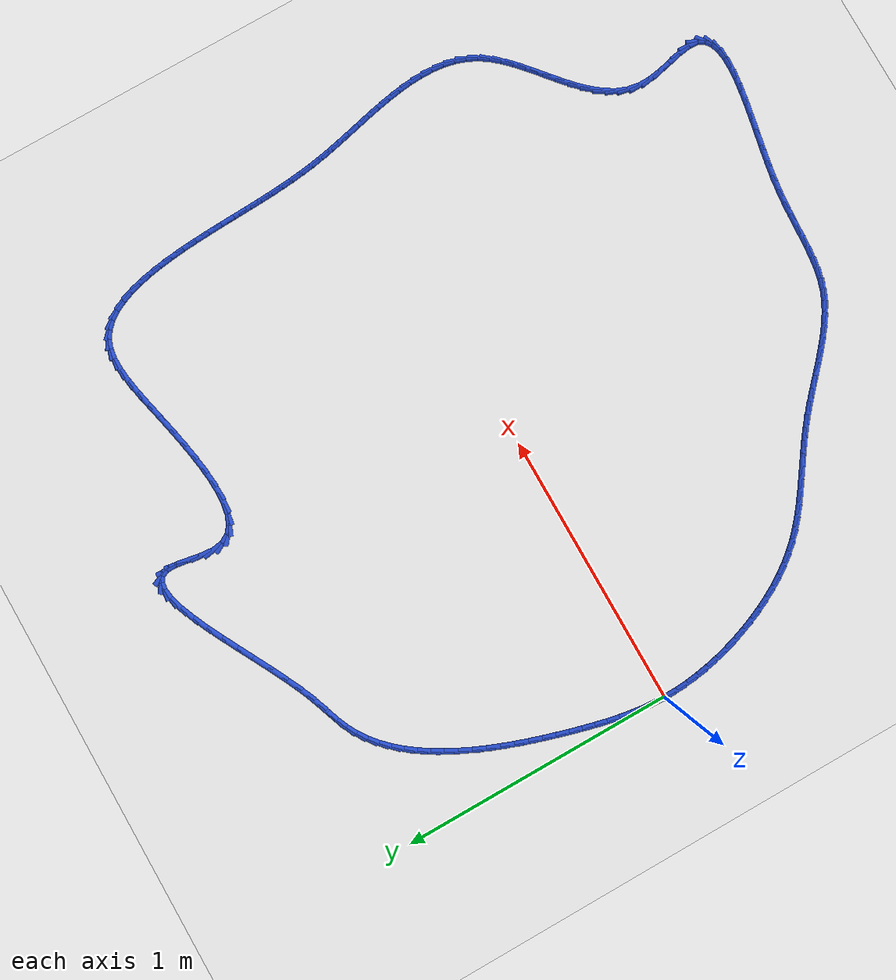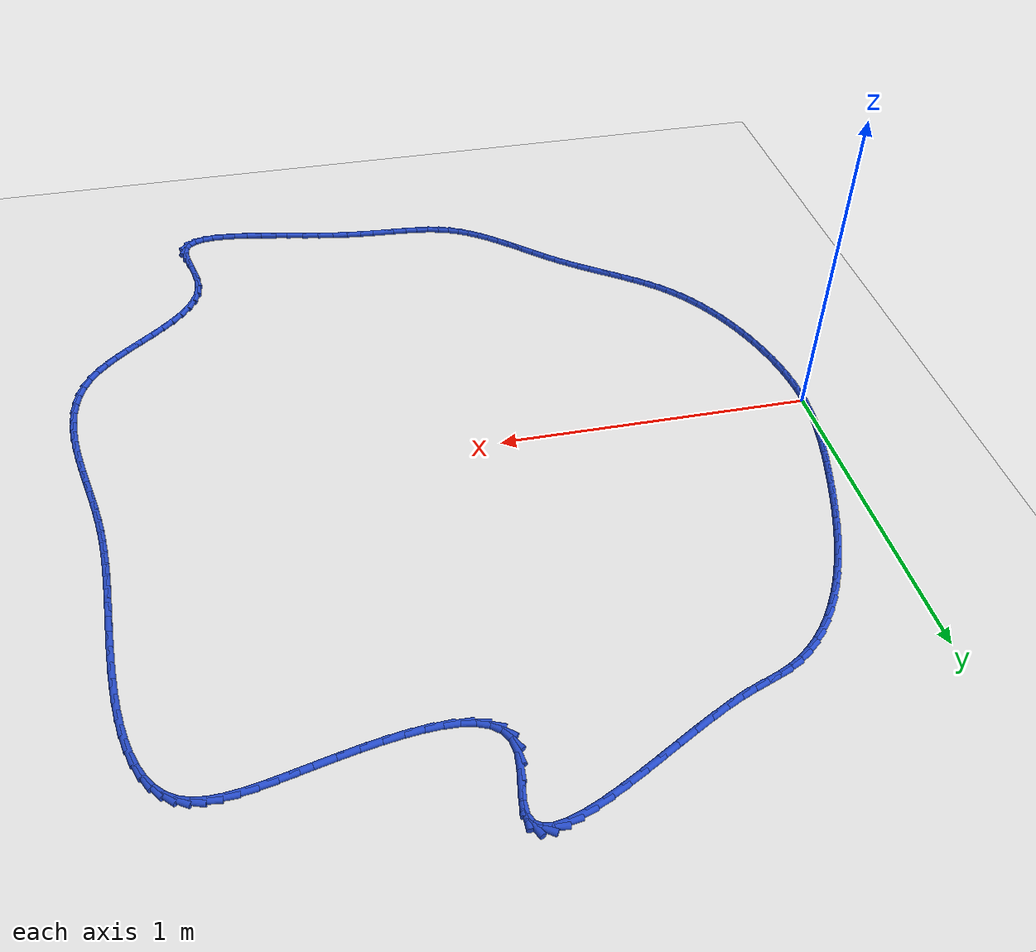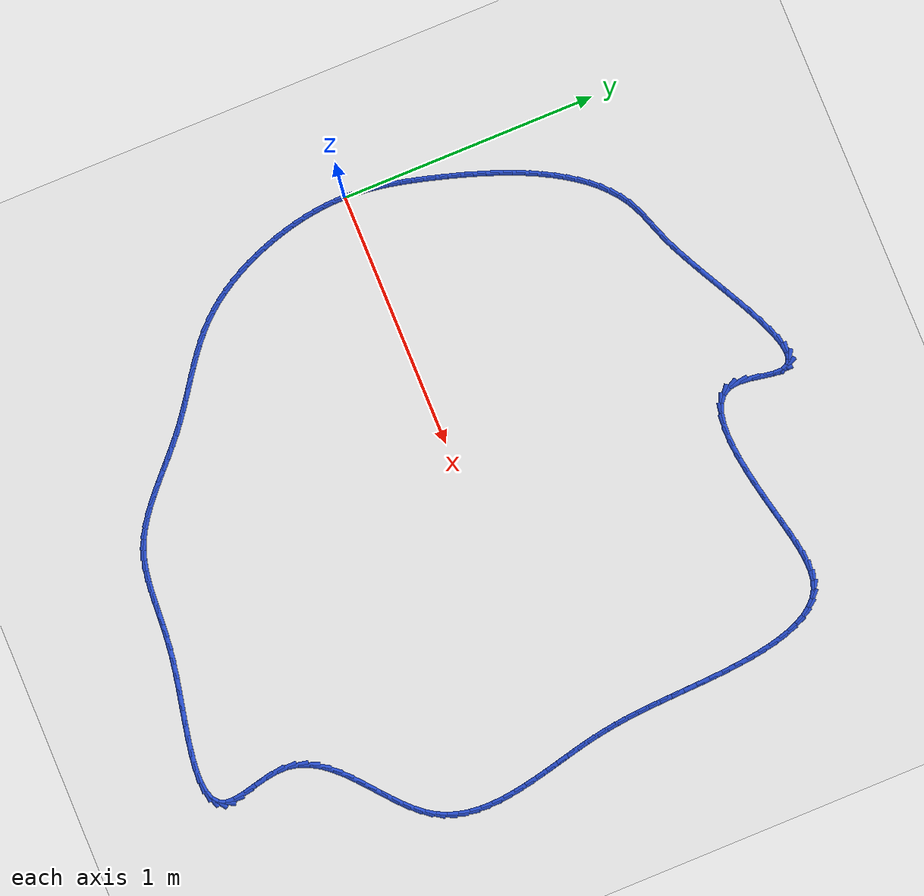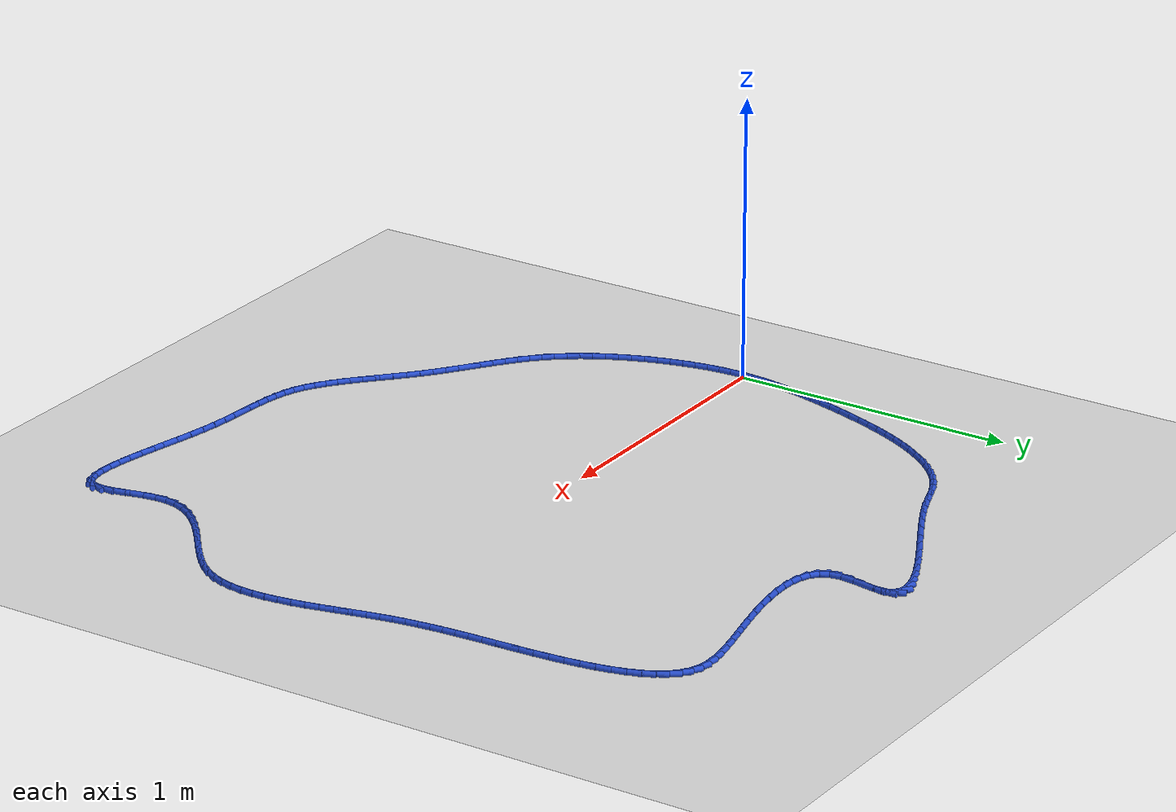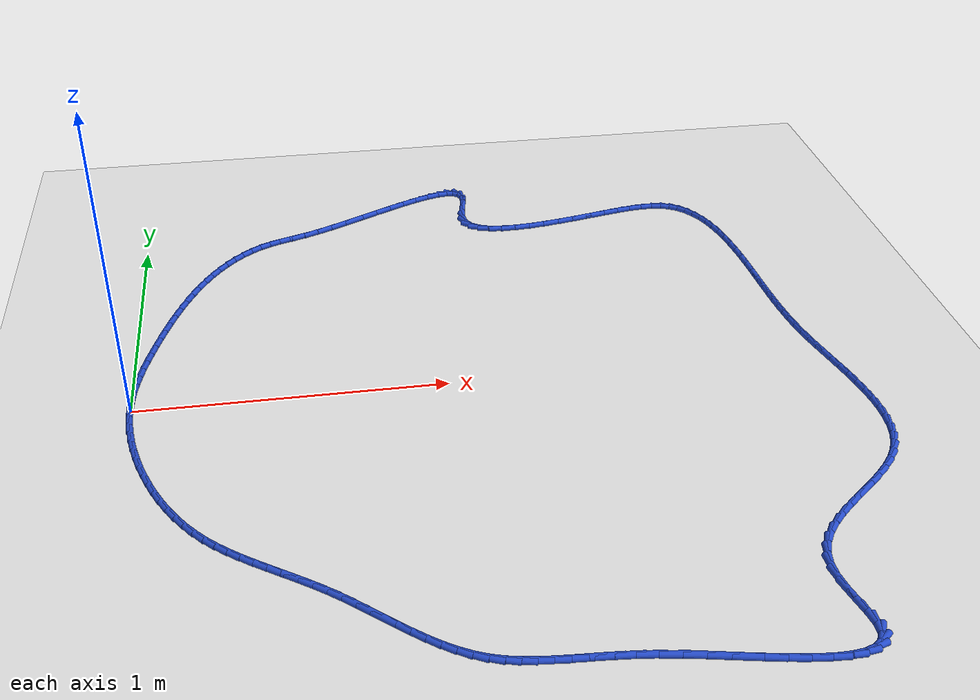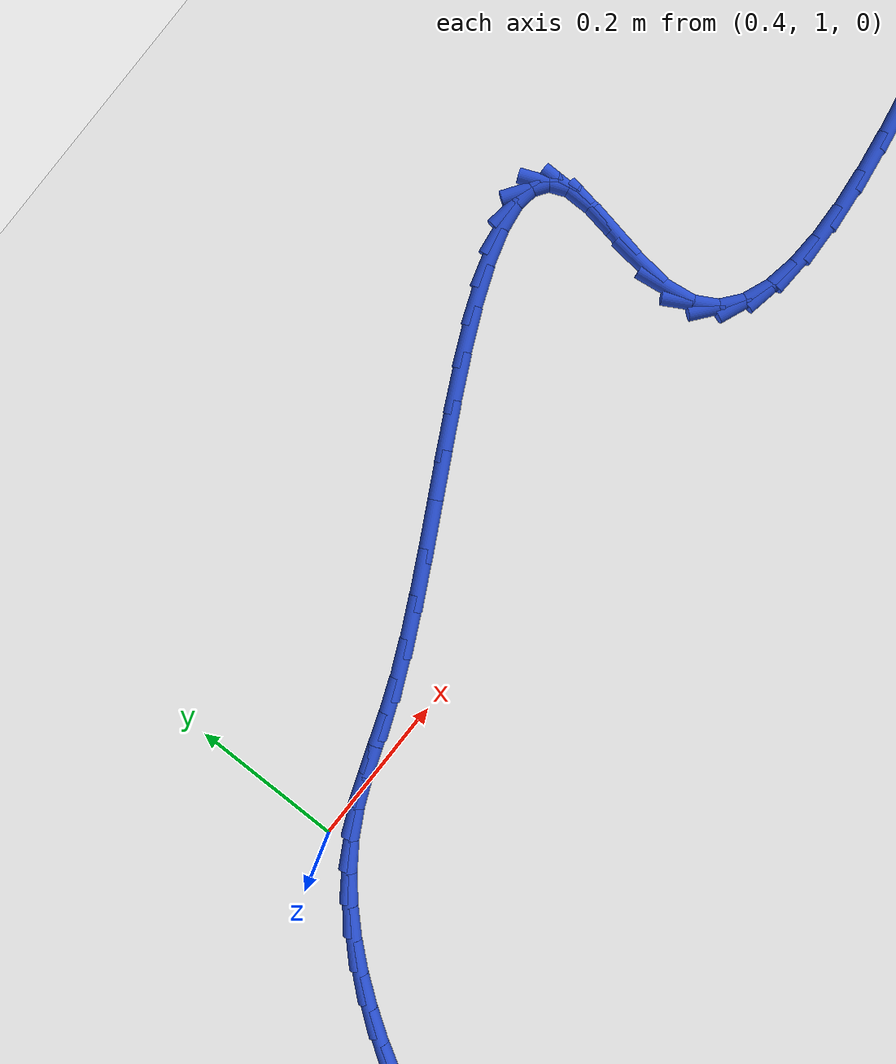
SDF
<sdf version="1.6">
 <world name="default">
  <light name="sun" type="directional">
   <pose>0 0 10 0 -0 0</pose>
   <diffuse>0.8 0.8 0.8 1</diffuse>
   <specular>0.2 0.2 0.2 1</specular>
   <attenuation>
    <range>1000</range>
    <constant>0.9</constant>
    <linear>0.01</linear>
    <quadratic>0.001</quadratic>
   </attenuation>
   <direction>-0.5 0.1 -0.9</direction>
  </light>
  <model name="ground_plane">
   <static>1</static>
   <link name="link">
    <collision name="collision">
     <geometry><plane><normal>0 0 1</normal><size>100 100</size></plane></geometry>
     <surface><friction><ode><mu>100</mu><mu2>50</mu2></ode></friction></surface>
    </collision>
    <visual name="visual">
     <cast_shadows>0</cast_shadows>
     <geometry><plane><normal>0 0 1</normal><size>100 100</size></plane></geometry>
     <material>
      <script><uri>file://media/materials/scripts/gazebo.material</uri><name>Gazebo/WhiteGlow</name></script>
     </material>
    </visual>
   </link>
  </model>
  <gravity>0 0 -9.8</gravity>
  <magnetic_field>6e-06 2.3e-05 -4.2e-05</magnetic_field>
  <atmosphere type="adiabatic"/>
  <physics name="default_physics" default="0" type="ode">
   <max_step_size>0.001</max_step_size>
   <real_time_factor>1</real_time_factor>
   <real_time_update_rate>1000</real_time_update_rate>
  </physics>
  <scene><ambient>0.4 0.4 0.4 1</ambient><background>0.7 0.7 0.7 1</background><shadows>1</shadows></scene>
  <spherical_coordinates>
   <surface_model>EARTH_WGS84</surface_model>
   <latitude_deg>0</latitude_deg>
   <longitude_deg>0</longitude_deg>
   <elevation>0</elevation>
   <heading_deg>0</heading_deg>
  </spherical_coordinates>
  <model name="line">
   <link name="link_0">
    <pose>-3.469446951953614e-18 1.1796119636642288e-16 0.01 0 1.57 1.5308132806313166</pose>
    <collision name="collision">
     <geometry><cylinder><radius>0.01</radius><length>0.08</length></cylinder></geometry>
    </collision>
    <visual name="visual">
     <material>
      <script><name>Gazebo/Blue</name><uri>file://media/materials/scripts/gazebo.material</uri></script>
     </material>
     <geometry><cylinder><radius>0.01</radius><length>0.08</length></cylinder></geometry>
    </visual>
   </link>
   <link name="link_1">
    <pose>0.0017337182763946626 0.04333822652563099 0.01 0 1.57 1.4814860341088028</pose>
    <collision name="collision">
     <geometry><cylinder><radius>0.01</radius><length>0.08</length></cylinder></geometry>
    </collision>
    <visual name="visual">
     <material>
      <script><name>Gazebo/Blue</name><uri>file://media/materials/scripts/gazebo.material</uri></script>
     </material>
     <geometry><cylinder><radius>0.01</radius><length>0.08</length></cylinder></geometry>
    </visual>
   </link>
   <link name="link_2">
    <pose>0.005598666395013631 0.0864986115429684 0.01 0 1.57 1.4371777145934055</pose>
    <collision name="collision">
     <geometry><cylinder><radius>0.01</radius><length>0.08</length></cylinder></geometry>
    </collision>
    <visual name="visual">
     <material>
      <script><name>Gazebo/Blue</name><uri>file://media/materials/scripts/gazebo.material</uri></script>
     </material>
     <geometry><cylinder><radius>0.01</radius><length>0.08</length></cylinder></geometry>
    </visual>
   </link>
   <link name="link_3">
    <pose>0.011393881295287298 0.12961150245784592 0.01 0 1.57 1.3983310384944785</pose>
    <collision name="collision">
     <geometry><cylinder><radius>0.01</radius><length>0.08</length></cylinder></geometry>
    </collision>
    <visual name="visual">
     <material>
      <script><name>Gazebo/Blue</name><uri>file://media/materials/scripts/gazebo.material</uri></script>
     </material>
     <geometry><cylinder><radius>0.01</radius><length>0.08</length></cylinder></geometry>
    </visual>
   </link>
   <link name="link_4">
    <pose>0.018918399916646053 0.17280724667609726 0.01 0 1.57 1.365194974533688</pose>
    <collision name="collision">
     <geometry><cylinder><radius>0.01</radius><length>0.08</length></cylinder></geometry>
    </collision>
    <visual name="visual">
     <material>
      <script><name>Gazebo/Blue</name><uri>file://media/materials/scripts/gazebo.material</uri></script>
     </material>
     <geometry><cylinder><radius>0.01</radius><length>0.08</length></cylinder></geometry>
    </visual>
   </link>
   <link name="link_5">
    <pose>0.027971259198520275 0.21621619160355593 0.01 0 1.57 1.3378541016218768</pose>
    <collision name="collision">
     <geometry><cylinder><radius>0.01</radius><length>0.08</length></cylinder></geometry>
    </collision>
    <visual name="visual">
     <material>
      <script><name>Gazebo/Blue</name><uri>file://media/materials/scripts/gazebo.material</uri></script>
     </material>
     <geometry><cylinder><radius>0.01</radius><length>0.08</length></cylinder></geometry>
    </visual>
   </link>
   <link name="link_6">
    <pose>0.03835149608034036 0.25996868464605555 0.01 0 1.57 1.3162632808387142</pose>
    <collision name="collision">
     <geometry><cylinder><radius>0.01</radius><length>0.08</length></cylinder></geometry>
    </collision>
    <visual name="visual">
     <material>
      <script><name>Gazebo/Blue</name><uri>file://media/materials/scripts/gazebo.material</uri></script>
     </material>
     <geometry><cylinder><radius>0.01</radius><length>0.08</length></cylinder></geometry>
    </visual>
   </link>
   <link name="link_7">
    <pose>0.049858147501536706 0.30419507320942984 0.01 0 1.57 1.300276334051858</pose>
    <collision name="collision">
     <geometry><cylinder><radius>0.01</radius><length>0.08</length></cylinder></geometry>
    </collision>
    <visual name="visual">
     <material>
      <script><name>Gazebo/Blue</name><uri>file://media/materials/scripts/gazebo.material</uri></script>
     </material>
     <geometry><cylinder><radius>0.01</radius><length>0.08</length></cylinder></geometry>
    </visual>
   </link>
   <link name="link_8">
    <pose>0.06229042117734544 0.3490254555384177 0.01 0 1.57 1.2876759069109418</pose>
    <collision name="collision">
     <geometry><cylinder><radius>0.01</radius><length>0.08</length></cylinder></geometry>
    </collision>
    <visual name="visual">
     <material>
      <script><name>Gazebo/Blue</name><uri>file://media/materials/scripts/gazebo.material</uri></script>
     </material>
     <geometry><cylinder><radius>0.01</radius><length>0.08</length></cylinder></geometry>
    </visual>
   </link>
   <link name="link_9">
    <pose>0.07551718816988037 0.39448829138348357 0.01 0 1.57 1.2732175549885287</pose>
    <collision name="collision">
     <geometry><cylinder><radius>0.01</radius><length>0.08</length></cylinder></geometry>
    </collision>
    <visual name="visual">
     <material>
      <script><name>Gazebo/Blue</name><uri>file://media/materials/scripts/gazebo.material</uri></script>
     </material>
     <geometry><cylinder><radius>0.01</radius><length>0.08</length></cylinder></geometry>
    </visual>
   </link>
   <link name="link_10">
    <pose>0.08958372965432737 0.4403546589727971 0.01 0 1.57 1.2559978482683956</pose>
    <collision name="collision">
     <geometry><cylinder><radius>0.01</radius><length>0.08</length></cylinder></geometry>
    </collision>
    <visual name="visual">
     <material>
      <script><name>Gazebo/Blue</name><uri>file://media/materials/scripts/gazebo.material</uri></script>
     </material>
     <geometry><cylinder><radius>0.01</radius><length>0.08</length></cylinder></geometry>
    </visual>
   </link>
   <link name="link_11">
    <pose>0.10456282826600449 0.48635551203400523 0.01 0 1.57 1.2358466229518055</pose>
    <collision name="collision">
     <geometry><cylinder><radius>0.01</radius><length>0.08</length></cylinder></geometry>
    </collision>
    <visual name="visual">
     <material>
      <script><name>Gazebo/Blue</name><uri>file://media/materials/scripts/gazebo.material</uri></script>
     </material>
     <geometry><cylinder><radius>0.01</radius><length>0.08</length></cylinder></geometry>
    </visual>
   </link>
   <link name="link_12">
    <pose>0.12052726664022984 0.5322218042947553 0.01 0 1.57 1.2125261020440539</pose>
    <collision name="collision">
     <geometry><cylinder><radius>0.01</radius><length>0.08</length></cylinder></geometry>
    </collision>
    <visual name="visual">
     <material>
      <script><name>Gazebo/Blue</name><uri>file://media/materials/scripts/gazebo.material</uri></script>
     </material>
     <geometry><cylinder><radius>0.01</radius><length>0.08</length></cylinder></geometry>
    </visual>
   </link>
   <link name="link_13">
    <pose>0.1375498274123215 0.5776844894826944 0.01 0 1.57 1.1857280870214235</pose>
    <collision name="collision">
     <geometry><cylinder><radius>0.01</radius><length>0.08</length></cylinder></geometry>
    </collision>
    <visual name="visual">
     <material>
      <script><name>Gazebo/Blue</name><uri>file://media/materials/scripts/gazebo.material</uri></script>
     </material>
     <geometry><cylinder><radius>0.01</radius><length>0.08</length></cylinder></geometry>
    </visual>
   </link>
   <link name="link_14">
    <pose>0.1557032932175975 0.6224745213254694 0.01 0 1.57 1.1550694259014196</pose>
    <collision name="collision">
     <geometry><cylinder><radius>0.01</radius><length>0.08</length></cylinder></geometry>
    </collision>
    <visual name="visual">
     <material>
      <script><name>Gazebo/Blue</name><uri>file://media/materials/scripts/gazebo.material</uri></script>
     </material>
     <geometry><cylinder><radius>0.01</radius><length>0.08</length></cylinder></geometry>
    </visual>
   </link>
   <link name="link_15">
    <pose>0.175060446691376 0.666322853550728 0.01 0 1.57 1.1200868528925287</pose>
    <collision name="collision">
     <geometry><cylinder><radius>0.01</radius><length>0.08</length></cylinder></geometry>
    </collision>
    <visual name="visual">
     <material>
      <script><name>Gazebo/Blue</name><uri>file://media/materials/scripts/gazebo.material</uri></script>
     </material>
     <geometry><cylinder><radius>0.01</radius><length>0.08</length></cylinder></geometry>
    </visual>
   </link>
   <link name="link_16">
    <pose>0.1956940704689749 0.7089604398861165 0.01 0 1.57 1.080232874510247</pose>
    <collision name="collision">
     <geometry><cylinder><radius>0.01</radius><length>0.08</length></cylinder></geometry>
    </collision>
    <visual name="visual">
     <material>
      <script><name>Gazebo/Blue</name><uri>file://media/materials/scripts/gazebo.material</uri></script>
     </material>
     <geometry><cylinder><radius>0.01</radius><length>0.08</length></cylinder></geometry>
    </visual>
   </link>
   <link name="link_17">
    <pose>0.21767694718571245 0.7501182340592825 0.01 0 1.57 1.034875441462953</pose>
    <collision name="collision">
     <geometry><cylinder><radius>0.01</radius><length>0.08</length></cylinder></geometry>
    </collision>
    <visual name="visual">
     <material>
      <script><name>Gazebo/Blue</name><uri>file://media/materials/scripts/gazebo.material</uri></script>
     </material>
     <geometry><cylinder><radius>0.01</radius><length>0.08</length></cylinder></geometry>
    </visual>
   </link>
   <link name="link_18">
    <pose>0.2410818594769067 0.7895271897978733 0.01 0 1.57 0.9833058500837129</pose>
    <collision name="collision">
     <geometry><cylinder><radius>0.01</radius><length>0.08</length></cylinder></geometry>
    </collision>
    <visual name="visual">
     <material>
      <script><name>Gazebo/Blue</name><uri>file://media/materials/scripts/gazebo.material</uri></script>
     </material>
     <geometry><cylinder><radius>0.01</radius><length>0.08</length></cylinder></geometry>
    </visual>
   </link>
   <link name="link_19">
    <pose>0.2659815899778757 0.8269182608295357 0.01 0 1.57 0.924761746532312</pose>
    <collision name="collision">
     <geometry><cylinder><radius>0.01</radius><length>0.08</length></cylinder></geometry>
    </collision>
    <visual name="visual">
     <material>
      <script><name>Gazebo/Blue</name><uri>file://media/materials/scripts/gazebo.material</uri></script>
     </material>
     <geometry><cylinder><radius>0.01</radius><length>0.08</length></cylinder></geometry>
    </visual>
   </link>
   <link name="link_20">
    <pose>0.2924489213239375 0.8620224008819166 0.01 0 1.57 0.8584750192438121</pose>
    <collision name="collision">
     <geometry><cylinder><radius>0.01</radius><length>0.08</length></cylinder></geometry>
    </collision>
    <visual name="visual">
     <material>
      <script><name>Gazebo/Blue</name><uri>file://media/materials/scripts/gazebo.material</uri></script>
     </material>
     <geometry><cylinder><radius>0.01</radius><length>0.08</length></cylinder></geometry>
    </visual>
   </link>
   <link name="link_21">
    <pose>0.32055663615041013 0.8945705636826639 0.01 0 1.57 0.7837566622476606</pose>
    <collision name="collision">
     <geometry><cylinder><radius>0.01</radius><length>0.08</length></cylinder></geometry>
    </collision>
    <visual name="visual">
     <material>
      <script><name>Gazebo/Blue</name><uri>file://media/materials/scripts/gazebo.material</uri></script>
     </material>
     <geometry><cylinder><radius>0.01</radius><length>0.08</length></cylinder></geometry>
    </visual>
   </link>
   <link name="link_22">
    <pose>0.3503775170926119 0.924293702959424 0.01 0 1.57 0.7001296184476679</pose>
    <collision name="collision">
     <geometry><cylinder><radius>0.01</radius><length>0.08</length></cylinder></geometry>
    </collision>
    <visual name="visual">
     <material>
      <script><name>Gazebo/Blue</name><uri>file://media/materials/scripts/gazebo.material</uri></script>
     </material>
     <geometry><cylinder><radius>0.01</radius><length>0.08</length></cylinder></geometry>
    </visual>
   </link>
   <link name="link_23">
    <pose>0.3819843467858606 0.9509227724398444 0.01 0 1.57 0.6075112259678378</pose>
    <collision name="collision">
     <geometry><cylinder><radius>0.01</radius><length>0.08</length></cylinder></geometry>
    </collision>
    <visual name="visual">
     <material>
      <script><name>Gazebo/Blue</name><uri>file://media/materials/scripts/gazebo.material</uri></script>
     </material>
     <geometry><cylinder><radius>0.01</radius><length>0.08</length></cylinder></geometry>
    </visual>
   </link>
   <link name="link_24">
    <pose>0.4154499078654743 0.9741887258515718 0.01 0 1.57 0.5064236134487557</pose>
    <collision name="collision">
     <geometry><cylinder><radius>0.01</radius><length>0.08</length></cylinder></geometry>
    </collision>
    <visual name="visual">
     <material>
      <script><name>Gazebo/Blue</name><uri>file://media/materials/scripts/gazebo.material</uri></script>
     </material>
     <geometry><cylinder><radius>0.01</radius><length>0.08</length></cylinder></geometry>
    </visual>
   </link>
   <link name="link_25">
    <pose>0.45084698296677145 0.9938225169222539 0.01 0 1.57 0.4067200654186166</pose>
    <collision name="collision">
     <geometry><cylinder><radius>0.01</radius><length>0.08</length></cylinder></geometry>
    </collision>
    <visual name="visual">
     <material>
      <script><name>Gazebo/Blue</name><uri>file://media/materials/scripts/gazebo.material</uri></script>
     </material>
     <geometry><cylinder><radius>0.01</radius><length>0.08</length></cylinder></geometry>
    </visual>
   </link>
   <link name="link_26">
    <pose>0.4883252506182559 1.0099658014967525 0.01 0 1.57 0.3499674653694926</pose>
    <collision name="collision">
     <geometry><cylinder><radius>0.01</radius><length>0.08</length></cylinder></geometry>
    </collision>
    <visual name="visual">
     <material>
      <script><name>Gazebo/Blue</name><uri>file://media/materials/scripts/gazebo.material</uri></script>
     </material>
     <geometry><cylinder><radius>0.01</radius><length>0.08</length></cylinder></geometry>
    </visual>
   </link>
   <link name="link_27">
    <pose>0.5283758405536133 1.0245839314208876 0.01 0 1.57 0.3457436856352865</pose>
    <collision name="collision">
     <geometry><cylinder><radius>0.01</radius><length>0.08</length></cylinder></geometry>
    </collision>
    <visual name="visual">
     <material>
      <script><name>Gazebo/Blue</name><uri>file://media/materials/scripts/gazebo.material</uri></script>
     </material>
     <geometry><cylinder><radius>0.01</radius><length>0.08</length></cylinder></geometry>
    </visual>
   </link>
   <link name="link_28">
    <pose>0.5715846241926494 1.0401482753050366 0.01 0 1.57 0.3837170176790657</pose>
    <collision name="collision">
     <geometry><cylinder><radius>0.01</radius><length>0.08</length></cylinder></geometry>
    </collision>
    <visual name="visual">
     <material>
      <script><name>Gazebo/Blue</name><uri>file://media/materials/scripts/gazebo.material</uri></script>
     </material>
     <geometry><cylinder><radius>0.01</radius><length>0.08</length></cylinder></geometry>
    </visual>
   </link>
   <link name="link_29">
    <pose>0.6185240442582641 1.0590990872372108 0.01 0 1.57 0.43199273822149525</pose>
    <collision name="collision">
     <geometry><cylinder><radius>0.01</radius><length>0.08</length></cylinder></geometry>
    </collision>
    <visual name="visual">
     <material>
      <script><name>Gazebo/Blue</name><uri>file://media/materials/scripts/gazebo.material</uri></script>
     </material>
     <geometry><cylinder><radius>0.01</radius><length>0.08</length></cylinder></geometry>
    </visual>
   </link>
   <link name="link_30">
    <pose>0.6691456111966975 1.0824374069320764 0.01 0 1.57 0.46394335242594864</pose>
    <collision name="collision">
     <geometry><cylinder><radius>0.01</radius><length>0.08</length></cylinder></geometry>
    </collision>
    <visual name="visual">
     <material>
      <script><name>Gazebo/Blue</name><uri>file://media/materials/scripts/gazebo.material</uri></script>
     </material>
     <geometry><cylinder><radius>0.01</radius><length>0.08</length></cylinder></geometry>
    </visual>
   </link>
   <link name="link_31">
    <pose>0.7225319325170912 1.1091503063285533 0.01 0 1.57 0.4828885834467119</pose>
    <collision name="collision">
     <geometry><cylinder><radius>0.01</radius><length>0.08</length></cylinder></geometry>
    </collision>
    <visual name="visual">
     <material>
      <script><name>Gazebo/Blue</name><uri>file://media/materials/scripts/gazebo.material</uri></script>
     </material>
     <geometry><cylinder><radius>0.01</radius><length>0.08</length></cylinder></geometry>
    </visual>
   </link>
   <link name="link_32">
    <pose>0.7777008273626576 1.1380746890606162 0.01 0 1.57 0.4916595472219491</pose>
    <collision name="collision">
     <geometry><cylinder><radius>0.01</radius><length>0.08</length></cylinder></geometry>
    </collision>
    <visual name="visual">
     <material>
      <script><name>Gazebo/Blue</name><uri>file://media/materials/scripts/gazebo.material</uri></script>
     </material>
     <geometry><cylinder><radius>0.01</radius><length>0.08</length></cylinder></geometry>
    </visual>
   </link>
   <link name="link_33">
    <pose>0.833670114876608 1.1680474587622391 0.01 0 1.57 0.491417717148591</pose>
    <collision name="collision">
     <geometry><cylinder><radius>0.01</radius><length>0.08</length></cylinder></geometry>
    </collision>
    <visual name="visual">
     <material>
      <script><name>Gazebo/Blue</name><uri>file://media/materials/scripts/gazebo.material</uri></script>
     </material>
     <geometry><cylinder><radius>0.01</radius><length>0.08</length></cylinder></geometry>
    </visual>
   </link>
   <link name="link_34">
    <pose>0.889457614202154 1.1979055190673955 0.01 0 1.57 0.48205246829047277</pose>
    <collision name="collision">
     <geometry><cylinder><radius>0.01</radius><length>0.08</length></cylinder></geometry>
    </collision>
    <visual name="visual">
     <material>
      <script><name>Gazebo/Blue</name><uri>file://media/materials/scripts/gazebo.material</uri></script>
     </material>
     <geometry><cylinder><radius>0.01</radius><length>0.08</length></cylinder></geometry>
    </visual>
   </link>
   <link name="link_35">
    <pose>0.9440811444825071 1.2264857736100603 0.01 0 1.57 0.4621320916891008</pose>
    <collision name="collision">
     <geometry><cylinder><radius>0.01</radius><length>0.08</length></cylinder></geometry>
    </collision>
    <visual name="visual">
     <material>
      <script><name>Gazebo/Blue</name><uri>file://media/materials/scripts/gazebo.material</uri></script>
     </material>
     <geometry><cylinder><radius>0.01</radius><length>0.08</length></cylinder></geometry>
    </visual>
   </link>
   <link name="link_36">
    <pose>0.9965585248608791 1.252625126024207 0.01 0 1.57 0.4283721390348129</pose>
    <collision name="collision">
     <geometry><cylinder><radius>0.01</radius><length>0.08</length></cylinder></geometry>
    </collision>
    <visual name="visual">
     <material>
      <script><name>Gazebo/Blue</name><uri>file://media/materials/scripts/gazebo.material</uri></script>
     </material>
     <geometry><cylinder><radius>0.01</radius><length>0.08</length></cylinder></geometry>
    </visual>
   </link>
   <link name="link_37">
    <pose>1.045907574480482 1.2751604799438092 0.01 0 1.57 0.3742565610275269</pose>
    <collision name="collision">
     <geometry><cylinder><radius>0.01</radius><length>0.08</length></cylinder></geometry>
    </collision>
    <visual name="visual">
     <material>
      <script><name>Gazebo/Blue</name><uri>file://media/materials/scripts/gazebo.material</uri></script>
     </material>
     <geometry><cylinder><radius>0.01</radius><length>0.08</length></cylinder></geometry>
    </visual>
   </link>
   <link name="link_38">
    <pose>1.0911461124845265 1.292928739002842 0.01 0 1.57 0.28674976524263324</pose>
    <collision name="collision">
     <geometry><cylinder><radius>0.01</radius><length>0.08</length></cylinder></geometry>
    </collision>
    <visual name="visual">
     <material>
      <script><name>Gazebo/Blue</name><uri>file://media/materials/scripts/gazebo.material</uri></script>
     </material>
     <geometry><cylinder><radius>0.01</radius><length>0.08</length></cylinder></geometry>
    </visual>
   </link>
   <link name="link_39">
    <pose>1.1312919580162253 1.304766806835279 0.01 0 1.57 0.13837172414238297</pose>
    <collision name="collision">
     <geometry><cylinder><radius>0.01</radius><length>0.08</length></cylinder></geometry>
    </collision>
    <visual name="visual">
     <material>
      <script><name>Gazebo/Blue</name><uri>file://media/materials/scripts/gazebo.material</uri></script>
     </material>
     <geometry><cylinder><radius>0.01</radius><length>0.08</length></cylinder></geometry>
    </visual>
   </link>
   <link name="link_40">
    <pose>1.1653629302187891 1.3095115870750935 0.01 0 1.57 -0.1292675187864802</pose>
    <collision name="collision">
     <geometry><cylinder><radius>0.01</radius><length>0.08</length></cylinder></geometry>
    </collision>
    <visual name="visual">
     <material>
      <script><name>Gazebo/Blue</name><uri>file://media/materials/scripts/gazebo.material</uri></script>
     </material>
     <geometry><cylinder><radius>0.01</radius><length>0.08</length></cylinder></geometry>
    </visual>
   </link>
   <link name="link_41">
    <pose>1.19237684823543 1.3059999833562606 0.01 0 1.57 -0.5981958094452218</pose>
    <collision name="collision">
     <geometry><cylinder><radius>0.01</radius><length>0.08</length></cylinder></geometry>
    </collision>
    <visual name="visual">
     <material>
      <script><name>Gazebo/Blue</name><uri>file://media/materials/scripts/gazebo.material</uri></script>
     </material>
     <geometry><cylinder><radius>0.01</radius><length>0.08</length></cylinder></geometry>
    </visual>
   </link>
   <link name="link_42">
    <pose>1.21135153120936 1.2930688993127541 0.01 0 1.57 -1.170368838219025</pose>
    <collision name="collision">
     <geometry><cylinder><radius>0.01</radius><length>0.08</length></cylinder></geometry>
    </collision>
    <visual name="visual">
     <material>
      <script><name>Gazebo/Blue</name><uri>file://media/materials/scripts/gazebo.material</uri></script>
     </material>
     <geometry><cylinder><radius>0.01</radius><length>0.08</length></cylinder></geometry>
    </visual>
   </link>
   <link name="link_43">
    <pose>1.2213047982837897 1.2695552385785476 0.01 0 1.57 -1.5660183303593078</pose>
    <collision name="collision">
     <geometry><cylinder><radius>0.01</radius><length>0.08</length></cylinder></geometry>
    </collision>
    <visual name="visual">
     <material>
      <script><name>Gazebo/Blue</name><uri>file://media/materials/scripts/gazebo.material</uri></script>
     </material>
     <geometry><cylinder><radius>0.01</radius><length>0.08</length></cylinder></geometry>
    </visual>
   </link>
   <link name="link_44">
    <pose>1.2214722191125873 1.2345155400308456 0.01 0 1.57 1.41578072529366</pose>
    <collision name="collision">
     <geometry><cylinder><radius>0.01</radius><length>0.08</length></cylinder></geometry>
    </collision>
    <visual name="visual">
     <material>
      <script><name>Gazebo/Blue</name><uri>file://media/materials/scripts/gazebo.material</uri></script>
     </material>
     <geometry><cylinder><radius>0.01</radius><length>0.08</length></cylinder></geometry>
    </visual>
   </link>
   <link name="link_45">
    <pose>1.21460159353411 1.1905489727272818 0.01 0 1.57 1.397124993248544</pose>
    <collision name="collision">
     <geometry><cylinder><radius>0.01</radius><length>0.08</length></cylinder></geometry>
    </collision>
    <visual name="visual">
     <material>
      <script><name>Gazebo/Blue</name><uri>file://media/materials/scripts/gazebo.material</uri></script>
     </material>
     <geometry><cylinder><radius>0.01</radius><length>0.08</length></cylinder></geometry>
    </visual>
   </link>
   <link name="link_46">
    <pose>1.206280561110654 1.1431191255912556 0.01 0 1.57 1.480575264627823</pose>
    <collision name="collision">
     <geometry><cylinder><radius>0.01</radius><length>0.08</length></cylinder></geometry>
    </collision>
    <visual name="visual">
     <material>
      <script><name>Gazebo/Blue</name><uri>file://media/materials/scripts/gazebo.material</uri></script>
     </material>
     <geometry><cylinder><radius>0.01</radius><length>0.08</length></cylinder></geometry>
    </visual>
   </link>
   <link name="link_47">
    <pose>1.2021781272937655 1.0977716576952683 0.01 0 1.57 -1.428299479856965</pose>
    <collision name="collision">
     <geometry><cylinder><radius>0.01</radius><length>0.08</length></cylinder></geometry>
    </collision>
    <visual name="visual">
     <material>
      <script><name>Gazebo/Blue</name><uri>file://media/materials/scripts/gazebo.material</uri></script>
     </material>
     <geometry><cylinder><radius>0.01</radius><length>0.08</length></cylinder></geometry>
    </visual>
   </link>
   <link name="link_48">
    <pose>1.207633482128626 1.0597470938440388 0.01 0 1.57 -1.0577176716662882</pose>
    <collision name="collision">
     <geometry><cylinder><radius>0.01</radius><length>0.08</length></cylinder></geometry>
    </collision>
    <visual name="visual">
     <material>
      <script><name>Gazebo/Blue</name><uri>file://media/materials/scripts/gazebo.material</uri></script>
     </material>
     <geometry><cylinder><radius>0.01</radius><length>0.08</length></cylinder></geometry>
    </visual>
   </link>
   <link name="link_49">
    <pose>1.2240368579263723 1.0306325142080293 0.01 0 1.57 -0.6774271405622254</pose>
    <collision name="collision">
     <geometry><cylinder><radius>0.01</radius><length>0.08</length></cylinder></geometry>
    </collision>
    <visual name="visual">
     <material>
      <script><name>Gazebo/Blue</name><uri>file://media/materials/scripts/gazebo.material</uri></script>
     </material>
     <geometry><cylinder><radius>0.01</radius><length>0.08</length></cylinder></geometry>
    </visual>
   </link>
   <link name="link_50">
    <pose>1.2501751532350187 1.0096064809616627 0.01 0 1.57 -0.3794046085265678</pose>
    <collision name="collision">
     <geometry><cylinder><radius>0.01</radius><length>0.08</length></cylinder></geometry>
    </collision>
    <visual name="visual">
     <material>
      <script><name>Gazebo/Blue</name><uri>file://media/materials/scripts/gazebo.material</uri></script>
     </material>
     <geometry><cylinder><radius>0.01</radius><length>0.08</length></cylinder></geometry>
    </visual>
   </link>
   <link name="link_51">
    <pose>1.2847893090233062 0.9958050378522942 0.01 0 1.57 -0.1760368268179505</pose>
    <collision name="collision">
     <geometry><cylinder><radius>0.01</radius><length>0.08</length></cylinder></geometry>
    </collision>
    <visual name="visual">
     <material>
      <script><name>Gazebo/Blue</name><uri>file://media/materials/scripts/gazebo.material</uri></script>
     </material>
     <geometry><cylinder><radius>0.01</radius><length>0.08</length></cylinder></geometry>
    </visual>
   </link>
   <link name="link_52">
    <pose>1.326620266259976 0.9883642286272787 0.01 0 1.57 -0.04065940591418247</pose>
    <collision name="collision">
     <geometry><cylinder><radius>0.01</radius><length>0.08</length></cylinder></geometry>
    </collision>
    <visual name="visual">
     <material>
      <script><name>Gazebo/Blue</name><uri>file://media/materials/scripts/gazebo.material</uri></script>
     </material>
     <geometry><cylinder><radius>0.01</radius><length>0.08</length></cylinder></geometry>
    </visual>
   </link>
   <link name="link_53">
    <pose>1.3744089659137666 0.9864200970339713 0.01 0 1.57 0.051178813620971625</pose>
    <collision name="collision">
     <geometry><cylinder><radius>0.01</radius><length>0.08</length></cylinder></geometry>
    </collision>
    <visual name="visual">
     <material>
      <script><name>Gazebo/Blue</name><uri>file://media/materials/scripts/gazebo.material</uri></script>
     </material>
     <geometry><cylinder><radius>0.01</radius><length>0.08</length></cylinder></geometry>
    </visual>
   </link>
   <link name="link_54">
    <pose>1.4268963489534197 0.9891086868197274 0.01 0 1.57 0.11495139839888693</pose>
    <collision name="collision">
     <geometry><cylinder><radius>0.01</radius><length>0.08</length></cylinder></geometry>
    </collision>
    <visual name="visual">
     <material>
      <script><name>Gazebo/Blue</name><uri>file://media/materials/scripts/gazebo.material</uri></script>
     </material>
     <geometry><cylinder><radius>0.01</radius><length>0.08</length></cylinder></geometry>
    </visual>
   </link>
   <link name="link_55">
    <pose>1.4828233563476758 0.9955660417319019 0.01 0 1.57 0.15974496204301103</pose>
    <collision name="collision">
     <geometry><cylinder><radius>0.01</radius><length>0.08</length></cylinder></geometry>
    </collision>
    <visual name="visual">
     <material>
      <script><name>Gazebo/Blue</name><uri>file://media/materials/scripts/gazebo.material</uri></script>
     </material>
     <geometry><cylinder><radius>0.01</radius><length>0.08</length></cylinder></geometry>
    </visual>
   </link>
   <link name="link_56">
    <pose>1.540930929065274 1.0049282055178506 0.01 0 1.57 0.19082573948042272</pose>
    <collision name="collision">
     <geometry><cylinder><radius>0.01</radius><length>0.08</length></cylinder></geometry>
    </collision>
    <visual name="visual">
     <material>
      <script><name>Gazebo/Blue</name><uri>file://media/materials/scripts/gazebo.material</uri></script>
     </material>
     <geometry><cylinder><radius>0.01</radius><length>0.08</length></cylinder></geometry>
    </visual>
   </link>
   <link name="link_57">
    <pose>1.599960008074955 1.0163312219249274 0.01 0 1.57 0.21114476324464695</pose>
    <collision name="collision">
     <geometry><cylinder><radius>0.01</radius><length>0.08</length></cylinder></geometry>
    </collision>
    <visual name="visual">
     <material>
      <script><name>Gazebo/Blue</name><uri>file://media/materials/scripts/gazebo.material</uri></script>
     </material>
     <geometry><cylinder><radius>0.01</radius><length>0.08</length></cylinder></geometry>
    </visual>
   </link>
   <link name="link_58">
    <pose>1.6586515343454602 1.0289111347004891 0.01 0 1.57 0.22208944850847645</pose>
    <collision name="collision">
     <geometry><cylinder><radius>0.01</radius><length>0.08</length></cylinder></geometry>
    </collision>
    <visual name="visual">
     <material>
      <script><name>Gazebo/Blue</name><uri>file://media/materials/scripts/gazebo.material</uri></script>
     </material>
     <geometry><cylinder><radius>0.01</radius><length>0.08</length></cylinder></geometry>
    </visual>
   </link>
   <link name="link_59">
    <pose>1.715746448845528 1.0418039875918894 0.01 0 1.57 0.22306281276324214</pose>
    <collision name="collision">
     <geometry><cylinder><radius>0.01</radius><length>0.08</length></cylinder></geometry>
    </collision>
    <visual name="visual">
     <material>
      <script><name>Gazebo/Blue</name><uri>file://media/materials/scripts/gazebo.material</uri></script>
     </material>
     <geometry><cylinder><radius>0.01</radius><length>0.08</length></cylinder></geometry>
    </visual>
   </link>
   <link name="link_60">
    <pose>1.770101598423419 1.0541337796189507 0.01 0 1.57 0.20827431880052827</pose>
    <collision name="collision">
     <geometry><cylinder><radius>0.01</radius><length>0.08</length></cylinder></geometry>
    </collision>
    <visual name="visual">
     <material>
      <script><name>Gazebo/Blue</name><uri>file://media/materials/scripts/gazebo.material</uri></script>
     </material>
     <geometry><cylinder><radius>0.01</radius><length>0.08</length></cylinder></geometry>
    </visual>
   </link>
   <link name="link_61">
    <pose>1.821284290645547 1.0649506800198731 0.01 0 1.57 0.17229365721245574</pose>
    <collision name="collision">
     <geometry><cylinder><radius>0.01</radius><length>0.08</length></cylinder></geometry>
    </collision>
    <visual name="visual">
     <material>
      <script><name>Gazebo/Blue</name><uri>file://media/materials/scripts/gazebo.material</uri></script>
     </material>
     <geometry><cylinder><radius>0.01</radius><length>0.08</length></cylinder></geometry>
    </visual>
   </link>
   <link name="link_62">
    <pose>1.8691308928843535 1.0732768978287042 0.01 0 1.57 0.10910229659935702</pose>
    <collision name="collision">
     <geometry><cylinder><radius>0.01</radius><length>0.08</length></cylinder></geometry>
    </collision>
    <visual name="visual">
     <material>
      <script><name>Gazebo/Blue</name><uri>file://media/materials/scripts/gazebo.material</uri></script>
     </material>
     <geometry><cylinder><radius>0.01</radius><length>0.08</length></cylinder></geometry>
    </visual>
   </link>
   <link name="link_63">
    <pose>1.9134782810071733 1.0781345892376304 0.01 0 1.57 0.01010954121117528</pose>
    <collision name="collision">
     <geometry><cylinder><radius>0.01</radius><length>0.08</length></cylinder></geometry>
    </collision>
    <visual name="visual">
     <material>
      <script><name>Gazebo/Blue</name><uri>file://media/materials/scripts/gazebo.material</uri></script>
     </material>
     <geometry><cylinder><radius>0.01</radius><length>0.08</length></cylinder></geometry>
    </visual>
   </link>
   <link name="link_64">
    <pose>1.9541633308813398 1.0785459104388369 0.01 0 1.57 -0.13517040338248948</pose>
    <collision name="collision">
     <geometry><cylinder><radius>0.01</radius><length>0.08</length></cylinder></geometry>
    </collision>
    <visual name="visual">
     <material>
      <script><name>Gazebo/Blue</name><uri>file://media/materials/scripts/gazebo.material</uri></script>
     </material>
     <geometry><cylinder><radius>0.01</radius><length>0.08</length></cylinder></geometry>
    </visual>
   </link>
   <link name="link_65">
    <pose>1.9910229183741894 1.0735330176245104 0.01 0 1.57 -0.3341734298260708</pose>
    <collision name="collision">
     <geometry><cylinder><radius>0.01</radius><length>0.08</length></cylinder></geometry>
    </collision>
    <visual name="visual">
     <material>
      <script><name>Gazebo/Blue</name><uri>file://media/materials/scripts/gazebo.material</uri></script>
     </material>
     <geometry><cylinder><radius>0.01</radius><length>0.08</length></cylinder></geometry>
    </visual>
   </link>
   <link name="link_66">
    <pose>2.02389450208353 1.0621201799384714 0.01 0 1.57 -0.5660249683826148</pose>
    <collision name="collision">
     <geometry><cylinder><radius>0.01</radius><length>0.08</length></cylinder></geometry>
    </collision>
    <visual name="visual">
     <material>
      <script><name>Gazebo/Blue</name><uri>file://media/materials/scripts/gazebo.material</uri></script>
     </material>
     <geometry><cylinder><radius>0.01</radius><length>0.08</length></cylinder></geometry>
    </visual>
   </link>
   <link name="link_67">
    <pose>2.05274223687525 1.0437910608740357 0.01 0 1.57 -0.7785474076196227</pose>
    <collision name="collision">
     <geometry><cylinder><radius>0.01</radius><length>0.08</length></cylinder></geometry>
    </collision>
    <visual name="visual">
     <material>
      <script><name>Gazebo/Blue</name><uri>file://media/materials/scripts/gazebo.material</uri></script>
     </material>
     <geometry><cylinder><radius>0.01</radius><length>0.08</length></cylinder></geometry>
    </visual>
   </link>
   <link name="link_68">
    <pose>2.0778145202552096 1.0190599735613888 0.01 0 1.57 -0.9546072466959705</pose>
    <collision name="collision">
     <geometry><cylinder><radius>0.01</radius><length>0.08</length></cylinder></geometry>
    </collision>
    <visual name="visual">
     <material>
      <script><name>Gazebo/Blue</name><uri>file://media/materials/scripts/gazebo.material</uri></script>
     </material>
     <geometry><cylinder><radius>0.01</radius><length>0.08</length></cylinder></geometry>
    </visual>
   </link>
   <link name="link_69">
    <pose>2.099398453582266 0.9885815693714465 0.01 0 1.57 -1.0938090799718307</pose>
    <collision name="collision">
     <geometry><cylinder><radius>0.01</radius><length>0.08</length></cylinder></geometry>
    </collision>
    <visual name="visual">
     <material>
      <script><name>Gazebo/Blue</name><uri>file://media/materials/scripts/gazebo.material</uri></script>
     </material>
     <geometry><cylinder><radius>0.01</radius><length>0.08</length></cylinder></geometry>
    </visual>
   </link>
   <link name="link_70">
    <pose>2.1177811382152743 0.9530104996751259 0.01 0 1.57 -1.2018724791066593</pose>
    <collision name="collision">
     <geometry><cylinder><radius>0.01</radius><length>0.08</length></cylinder></geometry>
    </collision>
    <visual name="visual">
     <material>
      <script><name>Gazebo/Blue</name><uri>file://media/materials/scripts/gazebo.material</uri></script>
     </material>
     <geometry><cylinder><radius>0.01</radius><length>0.08</length></cylinder></geometry>
    </visual>
   </link>
   <link name="link_71">
    <pose>2.13324967551309 0.9130014158433419 0.01 0 1.57 -1.2855571731825293</pose>
    <collision name="collision">
     <geometry><cylinder><radius>0.01</radius><length>0.08</length></cylinder></geometry>
    </collision>
    <visual name="visual">
     <material>
      <script><name>Gazebo/Blue</name><uri>file://media/materials/scripts/gazebo.material</uri></script>
     </material>
     <geometry><cylinder><radius>0.01</radius><length>0.08</length></cylinder></geometry>
    </visual>
   </link>
   <link name="link_72">
    <pose>2.14609116683457 0.8692089692470123 0.01 0 1.57 -1.3506123489635364</pose>
    <collision name="collision">
     <geometry><cylinder><radius>0.01</radius><length>0.08</length></cylinder></geometry>
    </collision>
    <visual name="visual">
     <material>
      <script><name>Gazebo/Blue</name><uri>file://media/materials/scripts/gazebo.material</uri></script>
     </material>
     <geometry><cylinder><radius>0.01</radius><length>0.08</length></cylinder></geometry>
    </visual>
   </link>
   <link name="link_73">
    <pose>2.156592713538569 0.8222878112570525 0.01 0 1.57 -1.401392696347992</pose>
    <collision name="collision">
     <geometry><cylinder><radius>0.01</radius><length>0.08</length></cylinder></geometry>
    </collision>
    <visual name="visual">
     <material>
      <script><name>Gazebo/Blue</name><uri>file://media/materials/scripts/gazebo.material</uri></script>
     </material>
     <geometry><cylinder><radius>0.01</radius><length>0.08</length></cylinder></geometry>
    </visual>
   </link>
   <link name="link_74">
    <pose>2.1650414169839447 0.7728925932443786 0.01 0 1.57 -1.4410401699863957</pose>
    <collision name="collision">
     <geometry><cylinder><radius>0.01</radius><length>0.08</length></cylinder></geometry>
    </collision>
    <visual name="visual">
     <material>
      <script><name>Gazebo/Blue</name><uri>file://media/materials/scripts/gazebo.material</uri></script>
     </material>
     <geometry><cylinder><radius>0.01</radius><length>0.08</length></cylinder></geometry>
    </visual>
   </link>
   <link name="link_75">
    <pose>2.1717243785295515 0.7216779665799076 0.01 0 1.57 -1.4717631658390051</pose>
    <collision name="collision">
     <geometry><cylinder><radius>0.01</radius><length>0.08</length></cylinder></geometry>
    </collision>
    <visual name="visual">
     <material>
      <script><name>Gazebo/Blue</name><uri>file://media/materials/scripts/gazebo.material</uri></script>
     </material>
     <geometry><cylinder><radius>0.01</radius><length>0.08</length></cylinder></geometry>
    </visual>
   </link>
   <link name="link_76">
    <pose>2.1769286995342467 0.6692985826345556 0.01 0 1.57 -1.495070344782296</pose>
    <collision name="collision">
     <geometry><cylinder><radius>0.01</radius><length>0.08</length></cylinder></geometry>
    </collision>
    <visual name="visual">
     <material>
      <script><name>Gazebo/Blue</name><uri>file://media/materials/scripts/gazebo.material</uri></script>
     </material>
     <geometry><cylinder><radius>0.01</radius><length>0.08</length></cylinder></geometry>
    </visual>
   </link>
   <link name="link_77">
    <pose>2.180941481356885 0.616409092779238 0.01 0 1.57 -1.5119328061815316</pose>
    <collision name="collision">
     <geometry><cylinder><radius>0.01</radius><length>0.08</length></cylinder></geometry>
    </collision>
    <visual name="visual">
     <material>
      <script><name>Gazebo/Blue</name><uri>file://media/materials/scripts/gazebo.material</uri></script>
     </material>
     <geometry><cylinder><radius>0.01</radius><length>0.08</length></cylinder></geometry>
    </visual>
   </link>
   <link name="link_78">
    <pose>2.1840498253563223 0.5636641483848724 0.01 0 1.57 -1.522879012066339</pose>
    <collision name="collision">
     <geometry><cylinder><radius>0.01</radius><length>0.08</length></cylinder></geometry>
    </collision>
    <visual name="visual">
     <material>
      <script><name>Gazebo/Blue</name><uri>file://media/materials/scripts/gazebo.material</uri></script>
     </material>
     <geometry><cylinder><radius>0.01</radius><length>0.08</length></cylinder></geometry>
    </visual>
   </link>
   <link name="link_79">
    <pose>2.1865408328914158 0.5117184008223746 0.01 0 1.57 -1.5280279847247782</pose>
    <collision name="collision">
     <geometry><cylinder><radius>0.01</radius><length>0.08</length></cylinder></geometry>
    </collision>
    <visual name="visual">
     <material>
      <script><name>Gazebo/Blue</name><uri>file://media/materials/scripts/gazebo.material</uri></script>
     </material>
     <geometry><cylinder><radius>0.01</radius><length>0.08</length></cylinder></geometry>
    </visual>
   </link>
   <link name="link_80">
    <pose>2.1887016053210204 0.46122650146266025 0.01 0 1.57 -1.5272361659839802</pose>
    <collision name="collision">
     <geometry><cylinder><radius>0.01</radius><length>0.08</length></cylinder></geometry>
    </collision>
    <visual name="visual">
     <material>
      <script><name>Gazebo/Blue</name><uri>file://media/materials/scripts/gazebo.material</uri></script>
     </material>
     <geometry><cylinder><radius>0.01</radius><length>0.08</length></cylinder></geometry>
    </visual>
   </link>
   <link name="link_81">
    <pose>2.1908131775494124 0.4127823162389064 0.01 0 1.57 -1.5217197132394809</pose>
    <collision name="collision">
     <geometry><cylinder><radius>0.01</radius><length>0.08</length></cylinder></geometry>
    </collision>
    <visual name="visual">
     <material>
      <script><name>Gazebo/Blue</name><uri>file://media/materials/scripts/gazebo.material</uri></script>
     </material>
     <geometry><cylinder><radius>0.01</radius><length>0.08</length></cylinder></geometry>
    </visual>
   </link>
   <link name="link_82">
    <pose>2.1930937459850255 0.36635007388410823 0.01 0 1.57 -1.5121822498236943</pose>
    <collision name="collision">
     <geometry><cylinder><radius>0.01</radius><length>0.08</length></cylinder></geometry>
    </collision>
    <visual name="visual">
     <material>
      <script><name>Gazebo/Blue</name><uri>file://media/materials/scripts/gazebo.material</uri></script>
     </material>
     <geometry><cylinder><radius>0.01</radius><length>0.08</length></cylinder></geometry>
    </visual>
   </link>
   <link name="link_83">
    <pose>2.195724339572399 0.32152158782133233 0.01 0 1.57 -1.498481643968661</pose>
    <collision name="collision">
     <geometry><cylinder><radius>0.01</radius><length>0.08</length></cylinder></geometry>
    </collision>
    <visual name="visual">
     <material>
      <script><name>Gazebo/Blue</name><uri>file://media/materials/scripts/gazebo.material</uri></script>
     </material>
     <geometry><cylinder><radius>0.01</radius><length>0.08</length></cylinder></geometry>
    </visual>
   </link>
   <link name="link_84">
    <pose>2.198885503133725 0.2778838206026253 0.01 0 1.57 -1.4806939934331027</pose>
    <collision name="collision">
     <geometry><cylinder><radius>0.01</radius><length>0.08</length></cylinder></geometry>
    </collision>
    <visual name="visual">
     <material>
      <script><name>Gazebo/Blue</name><uri>file://media/materials/scripts/gazebo.material</uri></script>
     </material>
     <geometry><cylinder><radius>0.01</radius><length>0.08</length></cylinder></geometry>
    </visual>
   </link>
   <link name="link_85">
    <pose>2.2027577814911976 0.23502373478003188 0.01 0 1.57 -1.459157759292304</pose>
    <collision name="collision">
     <geometry><cylinder><radius>0.01</radius><length>0.08</length></cylinder></geometry>
    </collision>
    <visual name="visual">
     <material>
      <script><name>Gazebo/Blue</name><uri>file://media/materials/scripts/gazebo.material</uri></script>
     </material>
     <geometry><cylinder><radius>0.01</radius><length>0.08</length></cylinder></geometry>
    </visual>
   </link>
   <link name="link_86">
    <pose>2.2075217194670076 0.19252829290559834 0.01 0 1.57 -1.4344677227691311</pose>
    <collision name="collision">
     <geometry><cylinder><radius>0.01</radius><length>0.08</length></cylinder></geometry>
    </collision>
    <visual name="visual">
     <material>
      <script><name>Gazebo/Blue</name><uri>file://media/materials/scripts/gazebo.material</uri></script>
     </material>
     <geometry><cylinder><radius>0.01</radius><length>0.08</length></cylinder></geometry>
    </visual>
   </link>
   <link name="link_87">
    <pose>2.21335786188335 0.14998445753136988 0.01 0 1.57 -1.4074276541994448</pose>
    <collision name="collision">
     <geometry><cylinder><radius>0.01</radius><length>0.08</length></cylinder></geometry>
    </collision>
    <visual name="visual">
     <material>
      <script><name>Gazebo/Blue</name><uri>file://media/materials/scripts/gazebo.material</uri></script>
     </material>
     <geometry><cylinder><radius>0.01</radius><length>0.08</length></cylinder></geometry>
    </visual>
   </link>
   <link name="link_88">
    <pose>2.2204467535624164 0.10697919120939167 0.01 0 1.57 -1.3790830893940322</pose>
    <collision name="collision">
     <geometry><cylinder><radius>0.01</radius><length>0.08</length></cylinder></geometry>
    </collision>
    <visual name="visual">
     <material>
      <script><name>Gazebo/Blue</name><uri>file://media/materials/scripts/gazebo.material</uri></script>
     </material>
     <geometry><cylinder><radius>0.01</radius><length>0.08</length></cylinder></geometry>
    </visual>
   </link>
   <link name="link_89">
    <pose>2.228962515747803 0.0631054534125606 0.01 0 1.57 -1.3550043156091547</pose>
    <collision name="collision">
     <geometry><cylinder><radius>0.01</radius><length>0.08</length></cylinder></geometry>
    </collision>
    <visual name="visual">
     <material>
      <script><name>Gazebo/Blue</name><uri>file://media/materials/scripts/gazebo.material</uri></script>
     </material>
     <geometry><cylinder><radius>0.01</radius><length>0.08</length></cylinder></geometry>
    </visual>
   </link>
   <link name="link_90">
    <pose>2.2388029068647475 0.018214210256399285 0.01 0 1.57 -1.341098192043429</pose>
    <collision name="collision">
     <geometry><cylinder><radius>0.01</radius><length>0.08</length></cylinder></geometry>
    </collision>
    <visual name="visual">
     <material>
      <script><name>Gazebo/Blue</name><uri>file://media/materials/scripts/gazebo.material</uri></script>
     </material>
     <geometry><cylinder><radius>0.01</radius><length>0.08</length></cylinder></geometry>
    </visual>
   </link>
   <link name="link_91">
    <pose>2.249490456114505 -0.027493265858255553 0.01 0 1.57 -1.336904773910523</pose>
    <collision name="collision">
     <geometry><cylinder><radius>0.01</radius><length>0.08</length></cylinder></geometry>
    </collision>
    <visual name="visual">
     <material>
      <script><name>Gazebo/Blue</name><uri>file://media/materials/scripts/gazebo.material</uri></script>
     </material>
     <geometry><cylinder><radius>0.01</radius><length>0.08</length></cylinder></geometry>
    </visual>
   </link>
   <link name="link_92">
    <pose>2.2605209142901437 -0.07379070275950123 0.01 0 1.57 -1.3419399847780724</pose>
    <collision name="collision">
     <geometry><cylinder><radius>0.01</radius><length>0.08</length></cylinder></geometry>
    </collision>
    <visual name="visual">
     <material>
      <script><name>Gazebo/Blue</name><uri>file://media/materials/scripts/gazebo.material</uri></script>
     </material>
     <geometry><cylinder><radius>0.01</radius><length>0.08</length></cylinder></geometry>
    </visual>
   </link>
   <link name="link_93">
    <pose>2.2713900321847316 -0.12045182827543237 0.01 0 1.57 -1.3561249875827166</pose>
    <collision name="collision">
     <geometry><cylinder><radius>0.01</radius><length>0.08</length></cylinder></geometry>
    </collision>
    <visual name="visual">
     <material>
      <script><name>Gazebo/Blue</name><uri>file://media/materials/scripts/gazebo.material</uri></script>
     </material>
     <geometry><cylinder><radius>0.01</radius><length>0.08</length></cylinder></geometry>
    </visual>
   </link>
   <link name="link_94">
    <pose>2.2815935605913404 -0.16725037023414643 0.01 0 1.57 -1.3797541491646406</pose>
    <collision name="collision">
     <geometry><cylinder><radius>0.01</radius><length>0.08</length></cylinder></geometry>
    </collision>
    <visual name="visual">
     <material>
      <script><name>Gazebo/Blue</name><uri>file://media/materials/scripts/gazebo.material</uri></script>
     </material>
     <geometry><cylinder><radius>0.01</radius><length>0.08</length></cylinder></geometry>
    </visual>
   </link>
   <link name="link_95">
    <pose>2.290627250303036 -0.21396005646373986 0.01 0 1.57 -1.4134764585083037</pose>
    <collision name="collision">
     <geometry><cylinder><radius>0.01</radius><length>0.08</length></cylinder></geometry>
    </collision>
    <visual name="visual">
     <material>
      <script><name>Gazebo/Blue</name><uri>file://media/materials/scripts/gazebo.material</uri></script>
     </material>
     <geometry><cylinder><radius>0.01</radius><length>0.08</length></cylinder></geometry>
    </visual>
   </link>
   <link name="link_96">
    <pose>2.2979868521128903 -0.26035461479230915 0.01 0 1.57 -1.4582767025828494</pose>
    <collision name="collision">
     <geometry><cylinder><radius>0.01</radius><length>0.08</length></cylinder></geometry>
    </collision>
    <visual name="visual">
     <material>
      <script><name>Gazebo/Blue</name><uri>file://media/materials/scripts/gazebo.material</uri></script>
     </material>
     <geometry><cylinder><radius>0.01</radius><length>0.08</length></cylinder></geometry>
    </visual>
   </link>
   <link name="link_97">
    <pose>2.3031681168139713 -0.30620777304795077 0.01 0 1.57 -1.5154320599389581</pose>
    <collision name="collision">
     <geometry><cylinder><radius>0.01</radius><length>0.08</length></cylinder></geometry>
    </collision>
    <visual name="visual">
     <material>
      <script><name>Gazebo/Blue</name><uri>file://media/materials/scripts/gazebo.material</uri></script>
     </material>
     <geometry><cylinder><radius>0.01</radius><length>0.08</length></cylinder></geometry>
    </visual>
   </link>
   <link name="link_98">
    <pose>2.3056667951993486 -0.3512932590587622 0.01 0 1.57 1.5551901301456426</pose>
    <collision name="collision">
     <geometry><cylinder><radius>0.01</radius><length>0.08</length></cylinder></geometry>
    </collision>
    <visual name="visual">
     <material>
      <script><name>Gazebo/Blue</name><uri>file://media/materials/scripts/gazebo.material</uri></script>
     </material>
     <geometry><cylinder><radius>0.01</radius><length>0.08</length></cylinder></geometry>
    </visual>
   </link>
   <link name="link_99">
    <pose>2.3049786380620914 -0.3953848006528381 0.01 0 1.57 1.4690008947099553</pose>
    <collision name="collision">
     <geometry><cylinder><radius>0.01</radius><length>0.08</length></cylinder></geometry>
    </collision>
    <visual name="visual">
     <material>
      <script><name>Gazebo/Blue</name><uri>file://media/materials/scripts/gazebo.material</uri></script>
     </material>
     <geometry><cylinder><radius>0.01</radius><length>0.08</length></cylinder></geometry>
    </visual>
   </link>
   <link name="link_100">
    <pose>2.3005993961952678 -0.4382561256582756 0.01 0 1.57 1.3666876034626838</pose>
    <collision name="collision">
     <geometry><cylinder><radius>0.01</radius><length>0.08</length></cylinder></geometry>
    </collision>
    <visual name="visual">
     <material>
      <script><name>Gazebo/Blue</name><uri>file://media/materials/scripts/gazebo.material</uri></script>
     </material>
     <geometry><cylinder><radius>0.01</radius><length>0.08</length></cylinder></geometry>
    </visual>
   </link>
   <link name="link_101">
    <pose>2.2920248203919487 -0.4796809619031716 0.01 0 1.57 1.2485145619801443</pose>
    <collision name="collision">
     <geometry><cylinder><radius>0.01</radius><length>0.08</length></cylinder></geometry>
    </collision>
    <visual name="visual">
     <material>
      <script><name>Gazebo/Blue</name><uri>file://media/materials/scripts/gazebo.material</uri></script>
     </material>
     <geometry><cylinder><radius>0.01</radius><length>0.08</length></cylinder></geometry>
    </visual>
   </link>
   <link name="link_102">
    <pose>2.278750661445202 -0.5194330372156223 0.01 0 1.57 1.1166729657357275</pose>
    <collision name="collision">
     <geometry><cylinder><radius>0.01</radius><length>0.08</length></cylinder></geometry>
    </collision>
    <visual name="visual">
     <material>
      <script><name>Gazebo/Blue</name><uri>file://media/materials/scripts/gazebo.material</uri></script>
     </material>
     <geometry><cylinder><radius>0.01</radius><length>0.08</length></cylinder></geometry>
    </visual>
   </link>
   <link name="link_103">
    <pose>2.260272670148097 -0.557286079423725 0.01 0 1.57 0.9794725065540709</pose>
    <collision name="collision">
     <geometry><cylinder><radius>0.01</radius><length>0.08</length></cylinder></geometry>
    </collision>
    <visual name="visual">
     <material>
      <script><name>Gazebo/Blue</name><uri>file://media/materials/scripts/gazebo.material</uri></script>
     </material>
     <geometry><cylinder><radius>0.01</radius><length>0.08</length></cylinder></geometry>
    </visual>
   </link>
   <link name="link_104">
    <pose>2.2362409357939055 -0.5930755684361447 0.01 0 1.57 0.8661509139422084</pose>
    <collision name="collision">
     <geometry><cylinder><radius>0.01</radius><length>0.08</length></cylinder></geometry>
    </collision>
    <visual name="visual">
     <material>
      <script><name>Gazebo/Blue</name><uri>file://media/materials/scripts/gazebo.material</uri></script>
     </material>
     <geometry><cylinder><radius>0.01</radius><length>0.08</length></cylinder></geometry>
    </visual>
   </link>
   <link name="link_105">
    <pose>2.207349748701378 -0.6270547774261755 0.01 0 1.57 0.7849653476040591</pose>
    <collision name="collision">
     <geometry><cylinder><radius>0.01</radius><length>0.08</length></cylinder></geometry>
    </collision>
    <visual name="visual">
     <material>
      <script><name>Gazebo/Blue</name><uri>file://media/materials/scripts/gazebo.material</uri></script>
     </material>
     <geometry><cylinder><radius>0.01</radius><length>0.08</length></cylinder></geometry>
    </visual>
   </link>
   <link name="link_106">
    <pose>2.174726165482497 -0.6596501328566182 0.01 0 1.57 0.7317744072201849</pose>
    <collision name="collision">
     <geometry><cylinder><radius>0.01</radius><length>0.08</length></cylinder></geometry>
    </collision>
    <visual name="visual">
     <material>
      <script><name>Gazebo/Blue</name><uri>file://media/materials/scripts/gazebo.material</uri></script>
     </material>
     <geometry><cylinder><radius>0.01</radius><length>0.08</length></cylinder></geometry>
    </visual>
   </link>
   <link name="link_107">
    <pose>2.139498633096479 -0.691288617479432 0.01 0 1.57 0.7030848901615386</pose>
    <collision name="collision">
     <geometry><cylinder><radius>0.01</radius><length>0.08</length></cylinder></geometry>
    </collision>
    <visual name="visual">
     <material>
      <script><name>Gazebo/Blue</name><uri>file://media/materials/scripts/gazebo.material</uri></script>
     </material>
     <geometry><cylinder><radius>0.01</radius><length>0.08</length></cylinder></geometry>
    </visual>
   </link>
   <link name="link_108">
    <pose>2.1027955985025386 -0.722397214046576 0.01 0 1.57 0.6968152362238429</pose>
    <collision name="collision">
     <geometry><cylinder><radius>0.01</radius><length>0.08</length></cylinder></geometry>
    </collision>
    <visual name="visual">
     <material>
      <script><name>Gazebo/Blue</name><uri>file://media/materials/scripts/gazebo.material</uri></script>
     </material>
     <geometry><cylinder><radius>0.01</radius><length>0.08</length></cylinder></geometry>
    </visual>
   </link>
   <link name="link_109">
    <pose>2.0657455086598913 -0.75340290531001 0.01 0 1.57 0.7124650124068238</pose>
    <collision name="collision">
     <geometry><cylinder><radius>0.01</radius><length>0.08</length></cylinder></geometry>
    </collision>
    <visual name="visual">
     <material>
      <script><name>Gazebo/Blue</name><uri>file://media/materials/scripts/gazebo.material</uri></script>
     </material>
     <geometry><cylinder><radius>0.01</radius><length>0.08</length></cylinder></geometry>
    </visual>
   </link>
   <link name="link_110">
    <pose>2.029476810527754 -0.7847326740216918 0.01 0 1.57 0.7511243950786164</pose>
    <collision name="collision">
     <geometry><cylinder><radius>0.01</radius><length>0.08</length></cylinder></geometry>
    </collision>
    <visual name="visual">
     <material>
      <script><name>Gazebo/Blue</name><uri>file://media/materials/scripts/gazebo.material</uri></script>
     </material>
     <geometry><cylinder><radius>0.01</radius><length>0.08</length></cylinder></geometry>
    </visual>
   </link>
   <link name="link_111">
    <pose>1.9951179510653427 -0.8168135029335816 0.01 0 1.57 0.8154033188375104</pose>
    <collision name="collision">
     <geometry><cylinder><radius>0.01</radius><length>0.08</length></cylinder></geometry>
    </collision>
    <visual name="visual">
     <material>
      <script><name>Gazebo/Blue</name><uri>file://media/materials/scripts/gazebo.material</uri></script>
     </material>
     <geometry><cylinder><radius>0.01</radius><length>0.08</length></cylinder></geometry>
    </visual>
   </link>
   <link name="link_112">
    <pose>1.9637973772318718 -0.8500723747976382 0.01 0 1.57 0.9090837387449837</pose>
    <collision name="collision">
     <geometry><cylinder><radius>0.01</radius><length>0.08</length></cylinder></geometry>
    </collision>
    <visual name="visual">
     <material>
      <script><name>Gazebo/Blue</name><uri>file://media/materials/scripts/gazebo.material</uri></script>
     </material>
     <geometry><cylinder><radius>0.01</radius><length>0.08</length></cylinder></geometry>
    </visual>
   </link>
   <link name="link_113">
    <pose>1.9366435359865577 -0.8849362723658211 0.01 0 1.57 1.0359531687558896</pose>
    <collision name="collision">
     <geometry><cylinder><radius>0.01</radius><length>0.08</length></cylinder></geometry>
    </collision>
    <visual name="visual">
     <material>
      <script><name>Gazebo/Blue</name><uri>file://media/materials/scripts/gazebo.material</uri></script>
     </material>
     <geometry><cylinder><radius>0.01</radius><length>0.08</length></cylinder></geometry>
    </visual>
   </link>
   <link name="link_114">
    <pose>1.9147848742886158 -0.9218321783900889 0.01 0 1.57 1.1970311399172846</pose>
    <collision name="collision">
     <geometry><cylinder><radius>0.01</radius><length>0.08</length></cylinder></geometry>
    </collision>
    <visual name="visual">
     <material>
      <script><name>Gazebo/Blue</name><uri>file://media/materials/scripts/gazebo.material</uri></script>
     </material>
     <geometry><cylinder><radius>0.01</radius><length>0.08</length></cylinder></geometry>
    </visual>
   </link>
   <link name="link_115">
    <pose>1.8993498390972625 -0.9611870756224027 0.01 0 1.57 1.3862993037774198</pose>
    <collision name="collision">
     <geometry><cylinder><radius>0.01</radius><length>0.08</length></cylinder></geometry>
    </collision>
    <visual name="visual">
     <material>
      <script><name>Gazebo/Blue</name><uri>file://media/materials/scripts/gazebo.material</uri></script>
     </material>
     <geometry><cylinder><radius>0.01</radius><length>0.08</length></cylinder></geometry>
    </visual>
   </link>
   <link name="link_116">
    <pose>1.8914668773717132 -1.0034279468147194 0.01 0 1.57 -1.556544511072082</pose>
    <collision name="collision">
     <geometry><cylinder><radius>0.01</radius><length>0.08</length></cylinder></geometry>
    </collision>
    <visual name="visual">
     <material>
      <script><name>Gazebo/Blue</name><uri>file://media/materials/scripts/gazebo.material</uri></script>
     </material>
     <geometry><cylinder><radius>0.01</radius><length>0.08</length></cylinder></geometry>
    </visual>
   </link>
   <link name="link_117">
    <pose>1.8921149504880403 -1.0488978890808849 0.01 0 1.57 -1.412225004125412</pose>
    <collision name="collision">
     <geometry><cylinder><radius>0.01</radius><length>0.08</length></cylinder></geometry>
    </collision>
    <visual name="visual">
     <material>
      <script><name>Gazebo/Blue</name><uri>file://media/materials/scripts/gazebo.material</uri></script>
     </material>
     <geometry><cylinder><radius>0.01</radius><length>0.08</length></cylinder></geometry>
    </visual>
   </link>
   <link name="link_118">
    <pose>1.8997291889292922 -1.0965124981447845 0.01 0 1.57 -1.3453929344066644</pose>
    <collision name="collision">
     <geometry><cylinder><radius>0.01</radius><length>0.08</length></cylinder></geometry>
    </collision>
    <visual name="visual">
     <material>
      <script><name>Gazebo/Blue</name><uri>file://media/materials/scripts/gazebo.material</uri></script>
     </material>
     <geometry><cylinder><radius>0.01</radius><length>0.08</length></cylinder></geometry>
    </visual>
   </link>
   <link name="link_119">
    <pose>1.9106164837456787 -1.1439930825011992 0.01 0 1.57 -1.343788448238945</pose>
    <collision name="collision">
     <geometry><cylinder><radius>0.01</radius><length>0.08</length></cylinder></geometry>
    </collision>
    <visual name="visual">
     <material>
      <script><name>Gazebo/Blue</name><uri>file://media/materials/scripts/gazebo.material</uri></script>
     </material>
     <geometry><cylinder><radius>0.01</radius><length>0.08</length></cylinder></geometry>
    </visual>
   </link>
   <link name="link_120">
    <pose>1.9210181886169333 -1.1890241735589382 0.01 0 1.57 -1.419052540230441</pose>
    <collision name="collision">
     <geometry><cylinder><radius>0.01</radius><length>0.08</length></cylinder></geometry>
    </collision>
    <visual name="visual">
     <material>
      <script><name>Gazebo/Blue</name><uri>file://media/materials/scripts/gazebo.material</uri></script>
     </material>
     <geometry><cylinder><radius>0.01</radius><length>0.08</length></cylinder></geometry>
    </visual>
   </link>
   <link name="link_121">
    <pose>1.9271756572227867 -1.2292903027268074 0.01 0 1.57 1.5157662019873384</pose>
    <collision name="collision">
     <geometry><cylinder><radius>0.01</radius><length>0.08</length></cylinder></geometry>
    </collision>
    <visual name="visual">
     <material>
      <script><name>Gazebo/Blue</name><uri>file://media/materials/scripts/gazebo.material</uri></script>
     </material>
     <geometry><cylinder><radius>0.01</radius><length>0.08</length></cylinder></geometry>
    </visual>
   </link>
   <link name="link_122">
    <pose>1.9253469849378135 -1.2624871378585003 0.01 0 1.57 1.1227106942761793</pose>
    <collision name="collision">
     <geometry><cylinder><radius>0.01</radius><length>0.08</length></cylinder></geometry>
    </collision>
    <visual name="visual">
     <material>
      <script><name>Gazebo/Blue</name><uri>file://media/materials/scripts/gazebo.material</uri></script>
     </material>
     <geometry><cylinder><radius>0.01</radius><length>0.08</length></cylinder></geometry>
    </visual>
   </link>
   <link name="link_123">
    <pose>1.9133852539751963 -1.2873713196176815 0.01 0 1.57 0.6795314769264146</pose>
    <collision name="collision">
     <geometry><cylinder><radius>0.01</radius><length>0.08</length></cylinder></geometry>
    </collision>
    <visual name="visual">
     <material>
      <script><name>Gazebo/Blue</name><uri>file://media/materials/scripts/gazebo.material</uri></script>
     </material>
     <geometry><cylinder><radius>0.01</radius><length>0.08</length></cylinder></geometry>
    </visual>
   </link>
   <link name="link_124">
    <pose>1.8920329948277521 -1.3046215271364874 0.01 0 1.57 0.33979442888530687</pose>
    <collision name="collision">
     <geometry><cylinder><radius>0.01</radius><length>0.08</length></cylinder></geometry>
    </collision>
    <visual name="visual">
     <material>
      <script><name>Gazebo/Blue</name><uri>file://media/materials/scripts/gazebo.material</uri></script>
     </material>
     <geometry><cylinder><radius>0.01</radius><length>0.08</length></cylinder></geometry>
    </visual>
   </link>
   <link name="link_125">
    <pose>1.8623373881038023 -1.3151190904287298 0.01 0 1.57 0.1244156111197588</pose>
    <collision name="collision">
     <geometry><cylinder><radius>0.01</radius><length>0.08</length></cylinder></geometry>
    </collision>
    <visual name="visual">
     <material>
      <script><name>Gazebo/Blue</name><uri>file://media/materials/scripts/gazebo.material</uri></script>
     </material>
     <geometry><cylinder><radius>0.01</radius><length>0.08</length></cylinder></geometry>
    </visual>
   </link>
   <link name="link_126">
    <pose>1.8253456144116673 -1.3197453395082204 0.01 0 1.57 -0.008411659280644038</pose>
    <collision name="collision">
     <geometry><cylinder><radius>0.01</radius><length>0.08</length></cylinder></geometry>
    </collision>
    <visual name="visual">
     <material>
      <script><name>Gazebo/Blue</name><uri>file://media/materials/scripts/gazebo.material</uri></script>
     </material>
     <geometry><cylinder><radius>0.01</radius><length>0.08</length></cylinder></geometry>
    </visual>
   </link>
   <link name="link_127">
    <pose>1.78210485435967 -1.319381604388771 0.01 0 1.57 -0.09206256556539884</pose>
    <collision name="collision">
     <geometry><cylinder><radius>0.01</radius><length>0.08</length></cylinder></geometry>
    </collision>
    <visual name="visual">
     <material>
      <script><name>Gazebo/Blue</name><uri>file://media/materials/scripts/gazebo.material</uri></script>
     </material>
     <geometry><cylinder><radius>0.01</radius><length>0.08</length></cylinder></geometry>
    </visual>
   </link>
   <link name="link_128">
    <pose>1.7336622885561306 -1.3149092150841928 0.01 0 1.57 -0.14535772827177787</pose>
    <collision name="collision">
     <geometry><cylinder><radius>0.01</radius><length>0.08</length></cylinder></geometry>
    </collision>
    <visual name="visual">
     <material>
      <script><name>Gazebo/Blue</name><uri>file://media/materials/scripts/gazebo.material</uri></script>
     </material>
     <geometry><cylinder><radius>0.01</radius><length>0.08</length></cylinder></geometry>
    </visual>
   </link>
   <link name="link_129">
    <pose>1.6810650976093708 -1.3072095016082987 0.01 0 1.57 -0.17842109518751503</pose>
    <collision name="collision">
     <geometry><cylinder><radius>0.01</radius><length>0.08</length></cylinder></geometry>
    </collision>
    <visual name="visual">
     <material>
      <script><name>Gazebo/Blue</name><uri>file://media/materials/scripts/gazebo.material</uri></script>
     </material>
     <geometry><cylinder><radius>0.01</radius><length>0.08</length></cylinder></geometry>
    </visual>
   </link>
   <link name="link_130">
    <pose>1.6253604621277116 -1.2971637939748988 0.01 0 1.57 -0.19668621668276895</pose>
    <collision name="collision">
     <geometry><cylinder><radius>0.01</radius><length>0.08</length></cylinder></geometry>
    </collision>
    <visual name="visual">
     <material>
      <script><name>Gazebo/Blue</name><uri>file://media/materials/scripts/gazebo.material</uri></script>
     </material>
     <geometry><cylinder><radius>0.01</radius><length>0.08</length></cylinder></geometry>
    </visual>
   </link>
   <link name="link_131">
    <pose>1.567595562719473 -1.2856534221978058 0.01 0 1.57 -0.2029204621627167</pose>
    <collision name="collision">
     <geometry><cylinder><radius>0.01</radius><length>0.08</length></cylinder></geometry>
    </collision>
    <visual name="visual">
     <material>
      <script><name>Gazebo/Blue</name><uri>file://media/materials/scripts/gazebo.material</uri></script>
     </material>
     <geometry><cylinder><radius>0.01</radius><length>0.08</length></cylinder></geometry>
    </visual>
   </link>
   <link name="link_132">
    <pose>1.5088175799929786 -1.2735597162908316 0.01 0 1.57 -0.19816365479531964</pose>
    <collision name="collision">
     <geometry><cylinder><radius>0.01</radius><length>0.08</length></cylinder></geometry>
    </collision>
    <visual name="visual">
     <material>
      <script><name>Gazebo/Blue</name><uri>file://media/materials/scripts/gazebo.material</uri></script>
     </material>
     <geometry><cylinder><radius>0.01</radius><length>0.08</length></cylinder></geometry>
    </visual>
   </link>
   <link name="link_133">
    <pose>1.4500736945565487 -1.2617640062677875 0.01 0 1.57 -0.1820731188608801</pose>
    <collision name="collision">
     <geometry><cylinder><radius>0.01</radius><length>0.08</length></cylinder></geometry>
    </collision>
    <visual name="visual">
     <material>
      <script><name>Gazebo/Blue</name><uri>file://media/materials/scripts/gazebo.material</uri></script>
     </material>
     <geometry><cylinder><radius>0.01</radius><length>0.08</length></cylinder></geometry>
    </visual>
   </link>
   <link name="link_134">
    <pose>1.3924110870185042 -1.2511476221424855 0.01 0 1.57 -0.15291051681293114</pose>
    <collision name="collision">
     <geometry><cylinder><radius>0.01</radius><length>0.08</length></cylinder></geometry>
    </collision>
    <visual name="visual">
     <material>
      <script><name>Gazebo/Blue</name><uri>file://media/materials/scripts/gazebo.material</uri></script>
     </material>
     <geometry><cylinder><radius>0.01</radius><length>0.08</length></cylinder></geometry>
    </visual>
   </link>
   <link name="link_135">
    <pose>1.3368744127831615 -1.2425886689545769 0.01 0 1.57 -0.11529196258769862</pose>
    <collision name="collision">
     <geometry><cylinder><radius>0.01</radius><length>0.08</length></cylinder></geometry>
    </collision>
    <visual name="visual">
     <material>
      <script><name>Gazebo/Blue</name><uri>file://media/materials/scripts/gazebo.material</uri></script>
     </material>
     <geometry><cylinder><radius>0.01</radius><length>0.08</length></cylinder></geometry>
    </visual>
   </link>
   <link name="link_136">
    <pose>1.2841286998038364 -1.2364804240951897 0.01 0 1.57 -0.08490712530675175</pose>
    <collision name="collision">
     <geometry><cylinder><radius>0.01</radius><length>0.08</length></cylinder></geometry>
    </collision>
    <visual name="visual">
     <material>
      <script><name>Gazebo/Blue</name><uri>file://media/materials/scripts/gazebo.material</uri></script>
     </material>
     <geometry><cylinder><radius>0.01</radius><length>0.08</length></cylinder></geometry>
    </visual>
   </link>
   <link name="link_137">
    <pose>1.234058041734694 -1.2322188225901618 0.01 0 1.57 -0.06589791376647325</pose>
    <collision name="collision">
     <geometry><cylinder><radius>0.01</radius><length>0.08</length></cylinder></geometry>
    </collision>
    <visual name="visual">
     <material>
      <script><name>Gazebo/Blue</name><uri>file://media/materials/scripts/gazebo.material</uri></script>
     </material>
     <geometry><cylinder><radius>0.01</radius><length>0.08</length></cylinder></geometry>
    </visual>
   </link>
   <link name="link_138">
    <pose>1.186450401322318 -1.2290770293080326 0.01 0 1.57 -0.06053051956634465</pose>
    <collision name="collision">
     <geometry><cylinder><radius>0.01</radius><length>0.08</length></cylinder></geometry>
    </collision>
    <visual name="visual">
     <material>
      <script><name>Gazebo/Blue</name><uri>file://media/materials/scripts/gazebo.material</uri></script>
     </material>
     <geometry><cylinder><radius>0.01</radius><length>0.08</length></cylinder></geometry>
    </visual>
   </link>
   <link name="link_139">
    <pose>1.14109374131329 -1.226328209117342 0.01 0 1.57 -0.07104469603447536</pose>
    <collision name="collision">
     <geometry><cylinder><radius>0.01</radius><length>0.08</length></cylinder></geometry>
    </collision>
    <visual name="visual">
     <material>
      <script><name>Gazebo/Blue</name><uri>file://media/materials/scripts/gazebo.material</uri></script>
     </material>
     <geometry><cylinder><radius>0.01</radius><length>0.08</length></cylinder></geometry>
    </visual>
   </link>
   <link name="link_140">
    <pose>1.0977760244541914 -1.2232455268866282 0.01 0 1.57 -0.09953259059481355</pose>
    <collision name="collision">
     <geometry><cylinder><radius>0.01</radius><length>0.08</length></cylinder></geometry>
    </collision>
    <visual name="visual">
     <material>
      <script><name>Gazebo/Blue</name><uri>file://media/materials/scripts/gazebo.material</uri></script>
     </material>
     <geometry><cylinder><radius>0.01</radius><length>0.08</length></cylinder></geometry>
    </visual>
   </link>
   <link name="link_141">
    <pose>1.0562852134916048 -1.2191021474844312 0.01 0 1.57 -0.14765165741157626</pose>
    <collision name="collision">
     <geometry><cylinder><radius>0.01</radius><length>0.08</length></cylinder></geometry>
    </collision>
    <visual name="visual">
     <material>
      <script><name>Gazebo/Blue</name><uri>file://media/materials/scripts/gazebo.material</uri></script>
     </material>
     <geometry><cylinder><radius>0.01</radius><length>0.08</length></cylinder></geometry>
    </visual>
   </link>
   <link name="link_142">
    <pose>1.016409271172111 -1.2131712357792899 0.01 0 1.57 -0.2160840326317428</pose>
    <collision name="collision">
     <geometry><cylinder><radius>0.01</radius><length>0.08</length></cylinder></geometry>
    </collision>
    <visual name="visual">
     <material>
      <script><name>Gazebo/Blue</name><uri>file://media/materials/scripts/gazebo.material</uri></script>
     </material>
     <geometry><cylinder><radius>0.01</radius><length>0.08</length></cylinder></geometry>
    </visual>
   </link>
   <link name="link_143">
    <pose>0.9779361602422945 -1.2047259566397432 0.01 0 1.57 -0.303758406248</pose>
    <collision name="collision">
     <geometry><cylinder><radius>0.01</radius><length>0.08</length></cylinder></geometry>
    </collision>
    <visual name="visual">
     <material>
      <script><name>Gazebo/Blue</name><uri>file://media/materials/scripts/gazebo.material</uri></script>
     </material>
     <geometry><cylinder><radius>0.01</radius><length>0.08</length></cylinder></geometry>
    </visual>
   </link>
   <link name="link_144">
    <pose>0.9406538434487355 -1.1930394749343312 0.01 0 1.57 -0.406626187821614</pose>
    <collision name="collision">
     <geometry><cylinder><radius>0.01</radius><length>0.08</length></cylinder></geometry>
    </collision>
    <visual name="visual">
     <material>
      <script><name>Gazebo/Blue</name><uri>file://media/materials/scripts/gazebo.material</uri></script>
     </material>
     <geometry><cylinder><radius>0.01</radius><length>0.08</length></cylinder></geometry>
    </visual>
   </link>
   <link name="link_145">
    <pose>0.9043511295954031 -1.1774065852792128 0.01 0 1.57 -0.5060905683559783</pose>
    <collision name="collision">
     <geometry><cylinder><radius>0.01</radius><length>0.08</length></cylinder></geometry>
    </collision>
    <visual name="visual">
     <material>
      <script><name>Gazebo/Blue</name><uri>file://media/materials/scripts/gazebo.material</uri></script>
     </material>
     <geometry><cylinder><radius>0.01</radius><length>0.08</length></cylinder></geometry>
    </visual>
   </link>
   <link name="link_146">
    <pose>0.8688404197471837 -1.1577252265428073 0.01 0 1.57 -0.5862144771242028</pose>
    <collision name="collision">
     <geometry><cylinder><radius>0.01</radius><length>0.08</length></cylinder></geometry>
    </collision>
    <visual name="visual">
     <material>
      <script><name>Gazebo/Blue</name><uri>file://media/materials/scripts/gazebo.material</uri></script>
     </material>
     <geometry><cylinder><radius>0.01</radius><length>0.08</length></cylinder></geometry>
    </visual>
   </link>
   <link name="link_147">
    <pose>0.8339602610218328 -1.1345617704139188 0.01 0 1.57 -0.6478978410372401</pose>
    <collision name="collision">
     <geometry><cylinder><radius>0.01</radius><length>0.08</length></cylinder></geometry>
    </collision>
    <visual name="visual">
     <material>
      <script><name>Gazebo/Blue</name><uri>file://media/materials/scripts/gazebo.material</uri></script>
     </material>
     <geometry><cylinder><radius>0.01</radius><length>0.08</length></cylinder></geometry>
    </visual>
   </link>
   <link name="link_148">
    <pose>0.7995505590448421 -1.1085173192981947 0.01 0 1.57 -0.6931478454338521</pose>
    <collision name="collision">
     <geometry><cylinder><radius>0.01</radius><length>0.08</length></cylinder></geometry>
    </collision>
    <visual name="visual">
     <material>
      <script><name>Gazebo/Blue</name><uri>file://media/materials/scripts/gazebo.material</uri></script>
     </material>
     <geometry><cylinder><radius>0.01</radius><length>0.08</length></cylinder></geometry>
    </visual>
   </link>
   <link name="link_149">
    <pose>0.7654512194417046 -1.0801929756012842 0.01 0 1.57 -0.7237749302502279</pose>
    <collision name="collision">
     <geometry><cylinder><radius>0.01</radius><length>0.08</length></cylinder></geometry>
    </collision>
    <visual name="visual">
     <material>
      <script><name>Gazebo/Blue</name><uri>file://media/materials/scripts/gazebo.material</uri></script>
     </material>
     <geometry><cylinder><radius>0.01</radius><length>0.08</length></cylinder></geometry>
    </visual>
   </link>
   <link name="link_150">
    <pose>0.7315021478379117 -1.050189841728834 0.01 0 1.57 -0.7411759560568328</pose>
    <collision name="collision">
     <geometry><cylinder><radius>0.01</radius><length>0.08</length></cylinder></geometry>
    </collision>
    <visual name="visual">
     <material>
      <script><name>Gazebo/Blue</name><uri>file://media/materials/scripts/gazebo.material</uri></script>
     </material>
     <geometry><cylinder><radius>0.01</radius><length>0.08</length></cylinder></geometry>
    </visual>
   </link>
   <link name="link_151">
    <pose>0.6975432498589561 -1.0191090200864925 0.01 0 1.57 -0.746271248208617</pose>
    <collision name="collision">
     <geometry><cylinder><radius>0.01</radius><length>0.08</length></cylinder></geometry>
    </collision>
    <visual name="visual">
     <material>
      <script><name>Gazebo/Blue</name><uri>file://media/materials/scripts/gazebo.material</uri></script>
     </material>
     <geometry><cylinder><radius>0.01</radius><length>0.08</length></cylinder></geometry>
    </visual>
   </link>
   <link name="link_152">
    <pose>0.6634144311303298 -0.9875516130799075 0.01 0 1.57 -0.7395074317150017</pose>
    <collision name="collision">
     <geometry><cylinder><radius>0.01</radius><length>0.08</length></cylinder></geometry>
    </collision>
    <visual name="visual">
     <material>
      <script><name>Gazebo/Blue</name><uri>file://media/materials/scripts/gazebo.material</uri></script>
     </material>
     <geometry><cylinder><radius>0.01</radius><length>0.08</length></cylinder></geometry>
    </visual>
   </link>
   <link name="link_153">
    <pose>0.628955597277525 -0.9561187231147266 0.01 0 1.57 -0.7208835326938372</pose>
    <collision name="collision">
     <geometry><cylinder><radius>0.01</radius><length>0.08</length></cylinder></geometry>
    </collision>
    <visual name="visual">
     <material>
      <script><name>Gazebo/Blue</name><uri>file://media/materials/scripts/gazebo.material</uri></script>
     </material>
     <geometry><cylinder><radius>0.01</radius><length>0.08</length></cylinder></geometry>
    </visual>
   </link>
   <link name="link_154">
    <pose>0.5940066539260331 -0.925411452596597 0.01 0 1.57 -0.6901536709021049</pose>
    <collision name="collision">
     <geometry><cylinder><radius>0.01</radius><length>0.08</length></cylinder></geometry>
    </collision>
    <visual name="visual">
     <material>
      <script><name>Gazebo/Blue</name><uri>file://media/materials/scripts/gazebo.material</uri></script>
     </material>
     <geometry><cylinder><radius>0.01</radius><length>0.08</length></cylinder></geometry>
    </visual>
   </link>
   <link name="link_155">
    <pose>0.5584107135131419 -0.8960236404520447 0.01 0 1.57 -0.6555647471850615</pose>
    <collision name="collision">
     <geometry><cylinder><radius>0.01</radius><length>0.08</length></cylinder></geometry>
    </collision>
    <visual name="visual">
     <material>
      <script><name>Gazebo/Blue</name><uri>file://media/materials/scripts/gazebo.material</uri></script>
     </material>
     <geometry><cylinder><radius>0.01</radius><length>0.08</length></cylinder></geometry>
    </visual>
   </link>
   <link name="link_156">
    <pose>0.5221815417129062 -0.8681625933436963 0.01 0 1.57 -0.6302984613815369</pose>
    <collision name="collision">
     <geometry><cylinder><radius>0.01</radius><length>0.08</length></cylinder></geometry>
    </collision>
    <visual name="visual">
     <material>
      <script><name>Gazebo/Blue</name><uri>file://media/materials/scripts/gazebo.material</uri></script>
     </material>
     <geometry><cylinder><radius>0.01</radius><length>0.08</length></cylinder></geometry>
    </visual>
   </link>
   <link name="link_157">
    <pose>0.48558561247536136 -0.8414632297165925 0.01 0 1.57 -0.6157577032878165</pose>
    <collision name="collision">
     <geometry><cylinder><radius>0.01</radius><length>0.08</length></cylinder></geometry>
    </collision>
    <visual name="visual">
     <material>
      <script><name>Gazebo/Blue</name><uri>file://media/materials/scripts/gazebo.material</uri></script>
     </material>
     <geometry><cylinder><radius>0.01</radius><length>0.08</length></cylinder></geometry>
    </visual>
   </link>
   <link name="link_158">
    <pose>0.44890981468282487 -0.8155142278732395 0.01 0 1.57 -0.6122300794846564</pose>
    <collision name="collision">
     <geometry><cylinder><radius>0.01</radius><length>0.08</length></cylinder></geometry>
    </collision>
    <visual name="visual">
     <material>
      <script><name>Gazebo/Blue</name><uri>file://media/materials/scripts/gazebo.material</uri></script>
     </material>
     <geometry><cylinder><radius>0.01</radius><length>0.08</length></cylinder></geometry>
    </visual>
   </link>
   <link name="link_159">
    <pose>0.4124410372176134 -0.7899042661161423 0.01 0 1.57 -0.619990073722379</pose>
    <collision name="collision">
     <geometry><cylinder><radius>0.01</radius><length>0.08</length></cylinder></geometry>
    </collision>
    <visual name="visual">
     <material>
      <script><name>Gazebo/Blue</name><uri>file://media/materials/scripts/gazebo.material</uri></script>
     </material>
     <geometry><cylinder><radius>0.01</radius><length>0.08</length></cylinder></geometry>
    </visual>
   </link>
   <link name="link_160">
    <pose>0.3764661689620455 -0.764222022747807 0.01 0 1.57 -0.6393108301637089</pose>
    <collision name="collision">
     <geometry><cylinder><radius>0.01</radius><length>0.08</length></cylinder></geometry>
    </collision>
    <visual name="visual">
     <material>
      <script><name>Gazebo/Blue</name><uri>file://media/materials/scripts/gazebo.material</uri></script>
     </material>
     <geometry><cylinder><radius>0.01</radius><length>0.08</length></cylinder></geometry>
    </visual>
   </link>
   <link name="link_161">
    <pose>0.3412720987984381 -0.7380561760707398 0.01 0 1.57 -0.6704319618846831</pose>
    <collision name="collision">
     <geometry><cylinder><radius>0.01</radius><length>0.08</length></cylinder></geometry>
    </collision>
    <visual name="visual">
     <material>
      <script><name>Gazebo/Blue</name><uri>file://media/materials/scripts/gazebo.material</uri></script>
     </material>
     <geometry><cylinder><radius>0.01</radius><length>0.08</length></cylinder></geometry>
    </visual>
   </link>
   <link name="link_162">
    <pose>0.3071457156091085 -0.7109954043874454 0.01 0 1.57 -0.7134767386335656</pose>
    <collision name="collision">
     <geometry><cylinder><radius>0.01</radius><length>0.08</length></cylinder></geometry>
    </collision>
    <visual name="visual">
     <material>
      <script><name>Gazebo/Blue</name><uri>file://media/materials/scripts/gazebo.material</uri></script>
     </material>
     <geometry><cylinder><radius>0.01</radius><length>0.08</length></cylinder></geometry>
    </visual>
   </link>
   <link name="link_163">
    <pose>0.27437390827637415 -0.6826283860004301 0.01 0 1.57 -0.7683164791974199</pose>
    <collision name="collision">
     <geometry><cylinder><radius>0.01</radius><length>0.08</length></cylinder></geometry>
    </collision>
    <visual name="visual">
     <material>
      <script><name>Gazebo/Blue</name><uri>file://media/materials/scripts/gazebo.material</uri></script>
     </material>
     <geometry><cylinder><radius>0.01</radius><length>0.08</length></cylinder></geometry>
    </visual>
   </link>
   <link name="link_164">
    <pose>0.24324356568255226 -0.6525437992121994 0.01 0 1.57 -0.8335516633757762</pose>
    <collision name="collision">
     <geometry><cylinder><radius>0.01</radius><length>0.08</length></cylinder></geometry>
    </collision>
    <visual name="visual">
     <material>
      <script><name>Gazebo/Blue</name><uri>file://media/materials/scripts/gazebo.material</uri></script>
     </material>
     <geometry><cylinder><radius>0.01</radius><length>0.08</length></cylinder></geometry>
    </visual>
   </link>
   <link name="link_165">
    <pose>0.21402352239582662 -0.6203648943612022 0.01 0 1.57 -0.8994325116833566</pose>
    <collision name="collision">
     <geometry><cylinder><radius>0.01</radius><length>0.08</length></cylinder></geometry>
    </collision>
    <visual name="visual">
     <material>
      <script><name>Gazebo/Blue</name><uri>file://media/materials/scripts/gazebo.material</uri></script>
     </material>
     <geometry><cylinder><radius>0.01</radius><length>0.08</length></cylinder></geometry>
    </visual>
   </link>
   <link name="link_166">
    <pose>0.18678919304781122 -0.5860852997991448 0.01 0 1.57 -0.9604920534406527</pose>
    <collision name="collision">
     <geometry><cylinder><radius>0.01</radius><length>0.08</length></cylinder></geometry>
    </collision>
    <visual name="visual">
     <material>
      <script><name>Gazebo/Blue</name><uri>file://media/materials/scripts/gazebo.material</uri></script>
     </material>
     <geometry><cylinder><radius>0.01</radius><length>0.08</length></cylinder></geometry>
    </visual>
   </link>
   <link name="link_167">
    <pose>0.1614986016047118 -0.5499234341563286 0.01 0 1.57 -1.016937878233526</pose>
    <collision name="collision">
     <geometry><cylinder><radius>0.01</radius><length>0.08</length></cylinder></geometry>
    </collision>
    <visual name="visual">
     <material>
      <script><name>Gazebo/Blue</name><uri>file://media/materials/scripts/gazebo.material</uri></script>
     </material>
     <geometry><cylinder><radius>0.01</radius><length>0.08</length></cylinder></geometry>
    </visual>
   </link>
   <link name="link_168">
    <pose>0.13810812250556517 -0.5121008747270839 0.01 0 1.57 -1.0691257795445193</pose>
    <collision name="collision">
     <geometry><cylinder><radius>0.01</radius><length>0.08</length></cylinder></geometry>
    </collision>
    <visual name="visual">
     <material>
      <script><name>Gazebo/Blue</name><uri>file://media/materials/scripts/gazebo.material</uri></script>
     </material>
     <geometry><cylinder><radius>0.01</radius><length>0.08</length></cylinder></geometry>
    </visual>
   </link>
   <link name="link_169">
    <pose>0.1165741301894079 -0.4728391988057402 0.01 0 1.57 -1.1174478912573205</pose>
    <collision name="collision">
     <geometry><cylinder><radius>0.01</radius><length>0.08</length></cylinder></geometry>
    </collision>
    <visual name="visual">
     <material>
      <script><name>Gazebo/Blue</name><uri>file://media/materials/scripts/gazebo.material</uri></script>
     </material>
     <geometry><cylinder><radius>0.01</radius><length>0.08</length></cylinder></geometry>
    </visual>
   </link>
   <link name="link_170">
    <pose>0.09685299909527646 -0.4323599836866271 0.01 0 1.57 -1.162308385288803</pose>
    <collision name="collision">
     <geometry><cylinder><radius>0.01</radius><length>0.08</length></cylinder></geometry>
    </collision>
    <visual name="visual">
     <material>
      <script><name>Gazebo/Blue</name><uri>file://media/materials/scripts/gazebo.material</uri></script>
     </material>
     <geometry><cylinder><radius>0.01</radius><length>0.08</length></cylinder></geometry>
    </visual>
   </link>
   <link name="link_171">
    <pose>0.07890110366220836 -0.3908848066640758 0.01 0 1.57 -1.20410807449912</pose>
    <collision name="collision">
     <geometry><cylinder><radius>0.01</radius><length>0.08</length></cylinder></geometry>
    </collision>
    <visual name="visual">
     <material>
      <script><name>Gazebo/Blue</name><uri>file://media/materials/scripts/gazebo.material</uri></script>
     </material>
     <geometry><cylinder><radius>0.01</radius><length>0.08</length></cylinder></geometry>
    </visual>
   </link>
   <link name="link_172">
    <pose>0.06267481832923985 -0.34863524503241544 0.01 0 1.57 -1.2435869914191517</pose>
    <collision name="collision">
     <geometry><cylinder><radius>0.01</radius><length>0.08</length></cylinder></geometry>
    </collision>
    <visual name="visual">
     <material>
      <script><name>Gazebo/Blue</name><uri>file://media/materials/scripts/gazebo.material</uri></script>
     </material>
     <geometry><cylinder><radius>0.01</radius><length>0.08</length></cylinder></geometry>
    </visual>
   </link>
   <link name="link_173">
    <pose>0.048143313948451526 -0.30582120140300445 0.01 0 1.57 -1.2833239559830556</pose>
    <collision name="collision">
     <geometry><cylinder><radius>0.01</radius><length>0.08</length></cylinder></geometry>
    </collision>
    <visual name="visual">
     <material>
      <script><name>Gazebo/Blue</name><uri>file://media/materials/scripts/gazebo.material</uri></script>
     </material>
     <geometry><cylinder><radius>0.01</radius><length>0.08</length></cylinder></geometry>
    </visual>
   </link>
   <link name="link_174">
    <pose>0.03535784489262153 -0.2625776902855083 0.01 0 1.57 -1.3244381426776026</pose>
    <collision name="collision">
     <geometry><cylinder><radius>0.01</radius><length>0.08</length></cylinder></geometry>
    </collision>
    <visual name="visual">
     <material>
      <script><name>Gazebo/Blue</name><uri>file://media/materials/scripts/gazebo.material</uri></script>
     </material>
     <geometry><cylinder><radius>0.01</radius><length>0.08</length></cylinder></geometry>
    </visual>
   </link>
   <link name="link_175">
    <pose>0.024402079848399937 -0.21901015330562054 0.01 0 1.57 -1.3671484898123323</pose>
    <collision name="collision">
     <geometry><cylinder><radius>0.01</radius><length>0.08</length></cylinder></geometry>
    </collision>
    <visual name="visual">
     <material>
      <script><name>Gazebo/Blue</name><uri>file://media/materials/scripts/gazebo.material</uri></script>
     </material>
     <geometry><cylinder><radius>0.01</radius><length>0.08</length></cylinder></geometry>
    </visual>
   </link>
   <link name="link_176">
    <pose>0.015359766964317487 -0.17522395959276013 0.01 0 1.57 -1.4116703313871686</pose>
    <collision name="collision">
     <geometry><cylinder><radius>0.01</radius><length>0.08</length></cylinder></geometry>
    </collision>
    <visual name="visual">
     <material>
      <script><name>Gazebo/Blue</name><uri>file://media/materials/scripts/gazebo.material</uri></script>
     </material>
     <geometry><cylinder><radius>0.01</radius><length>0.08</length></cylinder></geometry>
    </visual>
   </link>
   <link name="link_177">
    <pose>0.008314654388905475 -0.13132447827634863 0.01 0 1.57 -1.458214543964498</pose>
    <collision name="collision">
     <geometry><cylinder><radius>0.01</radius><length>0.08</length></cylinder></geometry>
    </collision>
    <visual name="visual">
     <material>
      <script><name>Gazebo/Blue</name><uri>file://media/materials/scripts/gazebo.material</uri></script>
     </material>
     <geometry><cylinder><radius>0.01</radius><length>0.08</length></cylinder></geometry>
    </visual>
   </link>
   <link name="link_178">
    <pose>0.0033504902706946015 -0.08741707848580485 0.01 0 1.57 -1.506982819308744</pose>
    <collision name="collision">
     <geometry><cylinder><radius>0.01</radius><length>0.08</length></cylinder></geometry>
    </collision>
    <visual name="visual">
     <material>
      <script><name>Gazebo/Blue</name><uri>file://media/materials/scripts/gazebo.material</uri></script>
     </material>
     <geometry><cylinder><radius>0.01</radius><length>0.08</length></cylinder></geometry>
    </visual>
   </link>
   <link name="link_179">
    <pose>0.0005510227582158 -0.04360712935054864 0.01 0 1.57 -1.5581609288241398</pose>
    <collision name="collision">
     <geometry><cylinder><radius>0.01</radius><length>0.08</length></cylinder></geometry>
    </collision>
    <visual name="visual">
     <material>
      <script><name>Gazebo/Blue</name><uri>file://media/materials/scripts/gazebo.material</uri></script>
     </material>
     <geometry><cylinder><radius>0.01</radius><length>0.08</length></cylinder></geometry>
    </visual>
   </link>
   <link name="link_180">
    <pose>-2.0816681711721685e-17 2.3592239273284576e-16 0.01 0 1.57 1.5296829314969573</pose>
    <collision name="collision">
     <geometry><cylinder><radius>0.01</radius><length>0.08</length></cylinder></geometry>
    </collision>
    <visual name="visual">
     <material>
      <script><name>Gazebo/Blue</name><uri>file://media/materials/scripts/gazebo.material</uri></script>
     </material>
     <geometry><cylinder><radius>0.01</radius><length>0.08</length></cylinder></geometry>
    </visual>
   </link>
   <link name="link_181">
    <pose>0.0017811701445780564 0.043298940436422045 0.01 0 1.57 1.5296829314969578</pose>
    <collision name="collision">
     <geometry><cylinder><radius>0.01</radius><length>0.08</length></cylinder></geometry>
    </collision>
    <visual name="visual">
     <material>
      <script><name>Gazebo/Blue</name><uri>file://media/materials/scripts/gazebo.material</uri></script>
     </material>
     <geometry><cylinder><radius>0.01</radius><length>0.08</length></cylinder></geometry>
    </visual>
   </link>
  </model>
 </world>
</sdf>
